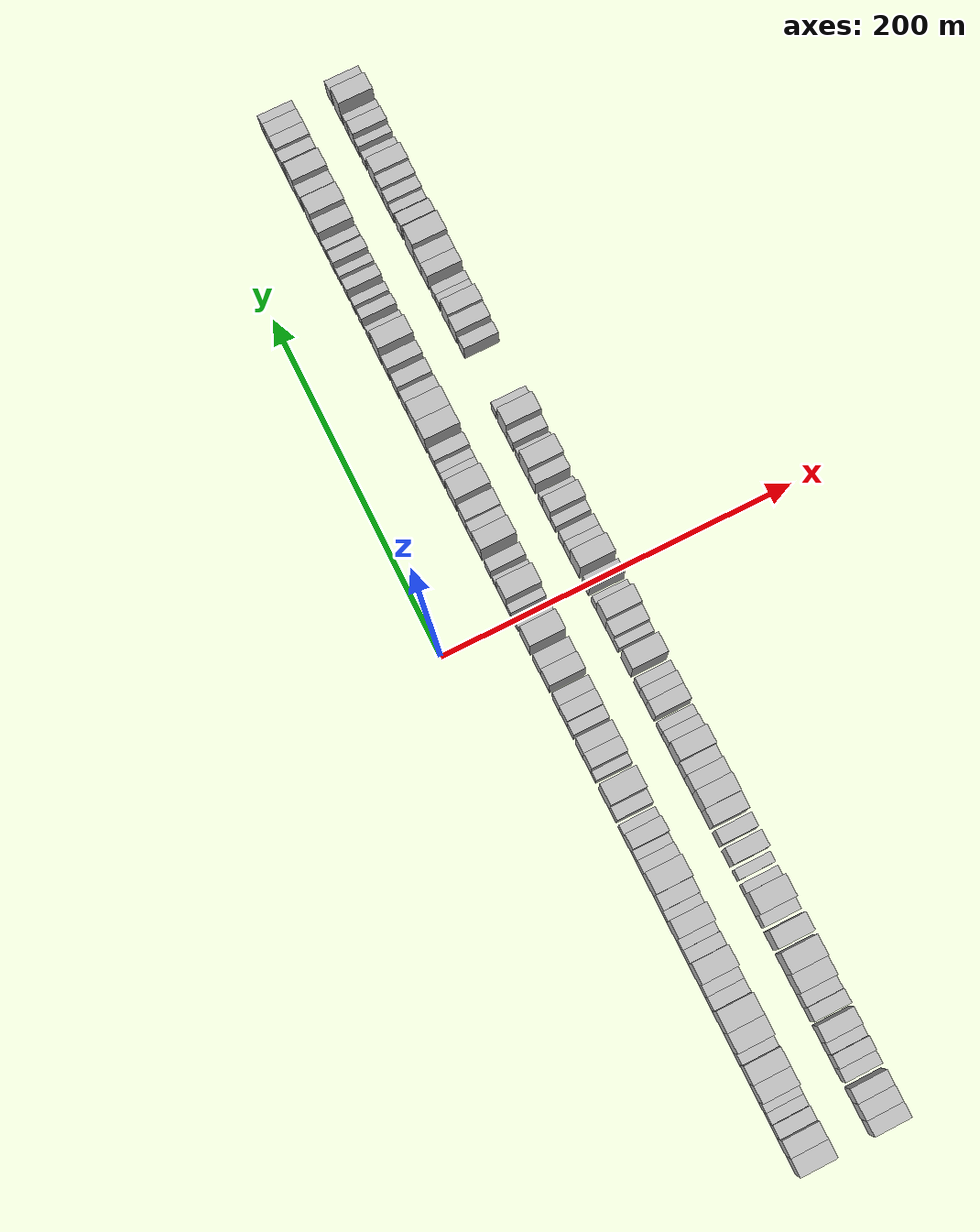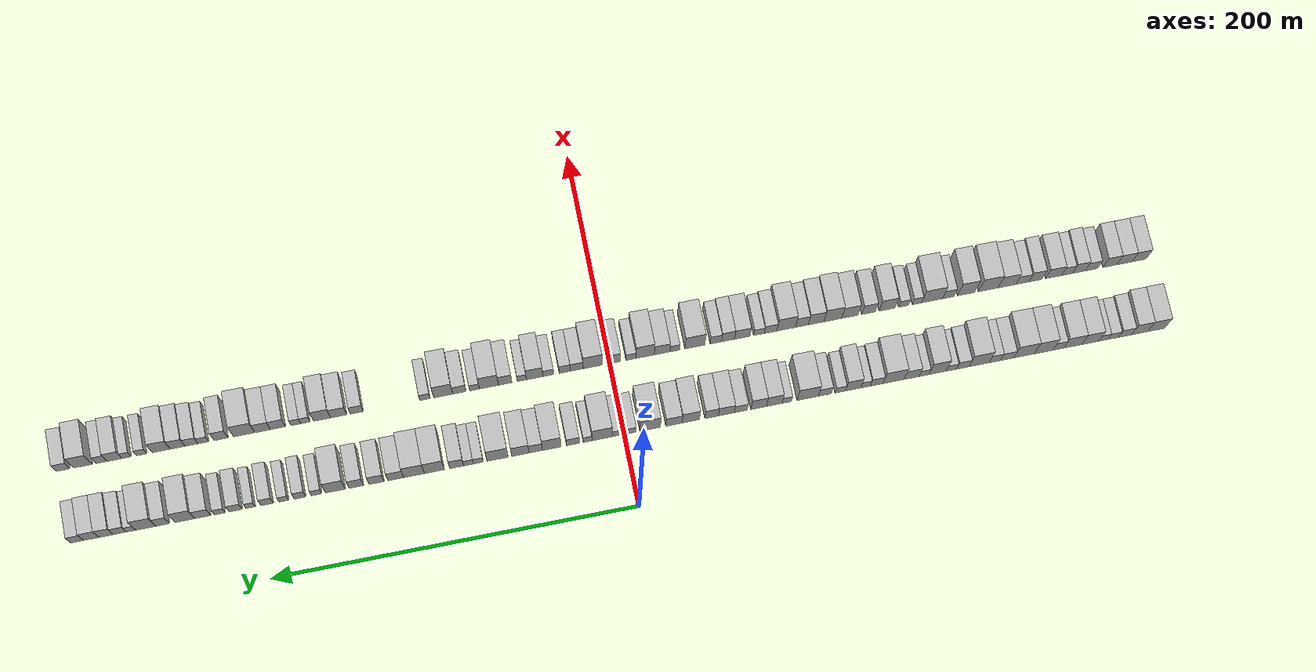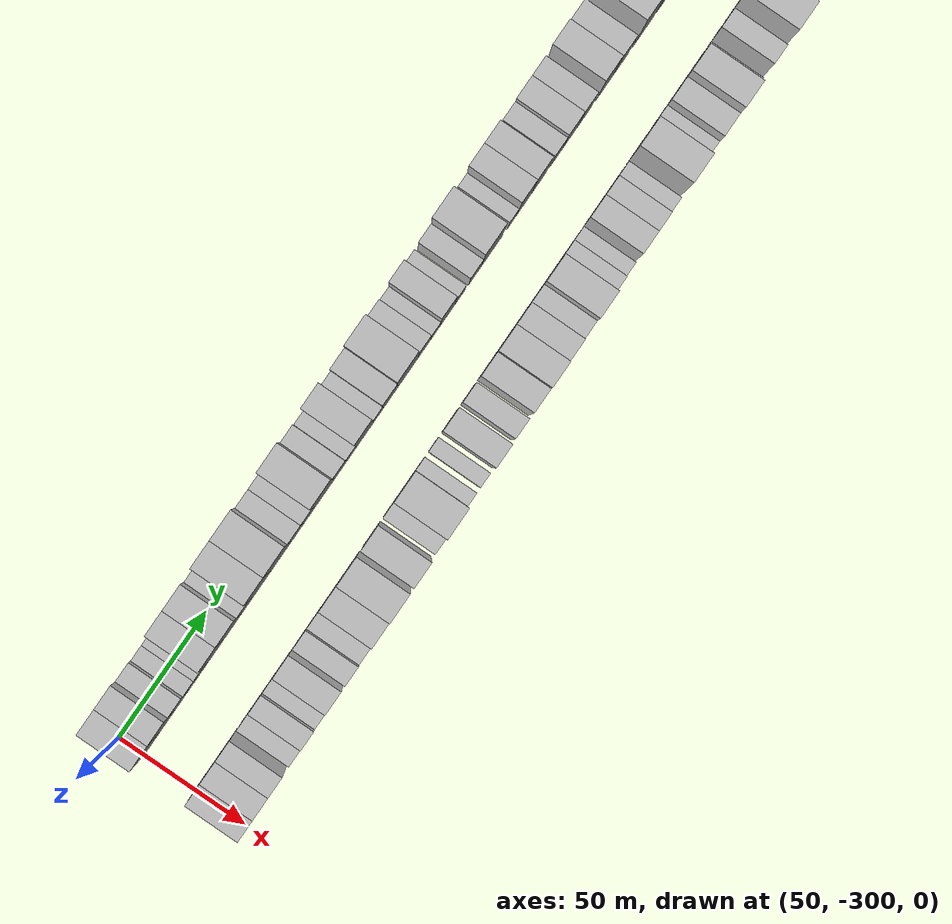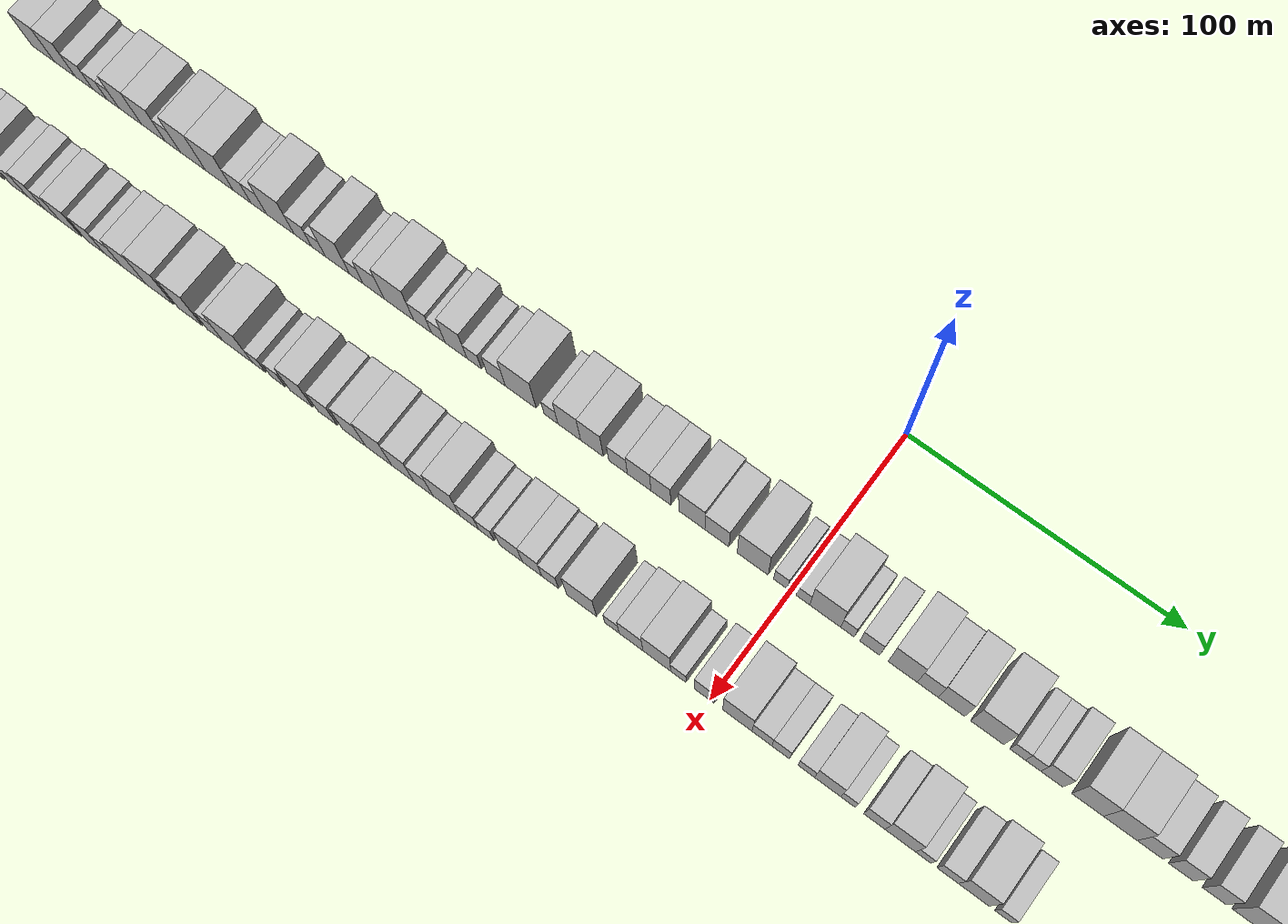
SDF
<sdf version="1.6">
 <world name="default">
  <scene>
   <sky><clouds><speed>12</speed></clouds></sky>
   <ambient>0.4 0.4 0.4 1</ambient>
   <background>0.7 0.7 0.7 1</background>
   <shadows>1</shadows>
  </scene>
  <gravity>0 0 -9.8066</gravity>
  <magnetic_field>6e-06 2.3e-05 -4.2e-05</magnetic_field>
  <physics default="0" name="default_physics" type="ode">
   <ode>
    <solver>
     <type>quick</type>
     <iters>10</iters>
     <sor>1.0</sor>
     <use_dynamic_moi_rescaling>0</use_dynamic_moi_rescaling>
    </solver>
    <constraints>
     <cfm>0</cfm>
     <erp>0.2</erp>
     <contact_max_correcting_vel>100</contact_max_correcting_vel>
     <contact_surface_layer>0.001</contact_surface_layer>
    </constraints>
   </ode>
   <max_step_size>0.004</max_step_size>
   <real_time_factor>1</real_time_factor>
   <real_time_update_rate>250</real_time_update_rate>
  </physics>
  <light name="sun" type="directional">
   <pose>0 0 10 0 0 0</pose>
   <diffuse>0.8 0.8 0.8 1</diffuse>
   <specular>0.2 0.2 0.2 1</specular>
   <attenuation>
    <range>1000</range>
    <constant>0.9</constant>
    <linear>0.01</linear>
    <quadratic>0.001</quadratic>
   </attenuation>
   <direction>-0.5 0.1 -0.9</direction>
  </light>
  <model name="building_1">
   <static>1</static>
   <pose>50.0000 -295.1970 0 0.000000 0.000000 0.000000</pose>
   <link name="link">
    <pose>0 0 10.50 0 0 0</pose>
    <collision name="collision"><geometry><box><size>20.0000 9.6060 21.0000</size></box></geometry></collision>
    <visual name="visual">
     <cast_shadows>0</cast_shadows>
     <geometry><box><size>20.0000 9.6060 21.0000</size></box></geometry>
     <material>
      <script>
       <uri>model://HANNAS_wall/materials/scripts</uri>
       <uri>model://HANNAS_wall/materials/textures</uri>
       <name>vrc/HANNAS_wall</name>
      </script>
     </material>
    </visual>
   </link>
  </model>
  <model name="building_2">
   <static>1</static>
   <pose>50.0000 -285.8825 0 0.000000 0.000000 0.000000</pose>
   <link name="link">
    <pose>0 0 10.50 0 0 0</pose>
    <collision name="collision"><geometry><box><size>20.0000 9.0231 21.0000</size></box></geometry></collision>
    <visual name="visual">
     <cast_shadows>0</cast_shadows>
     <geometry><box><size>20.0000 9.0231 21.0000</size></box></geometry>
     <material>
      <script>
       <uri>model://HANNAS_wall/materials/scripts</uri>
       <uri>model://HANNAS_wall/materials/textures</uri>
       <name>vrc/HANNAS_wall</name>
      </script>
     </material>
    </visual>
   </link>
  </model>
  <model name="building_3">
   <static>1</static>
   <pose>50.0000 -277.6992 0 0.000000 0.000000 0.000000</pose>
   <link name="link">
    <pose>0 0 7.50 0 0 0</pose>
    <collision name="collision"><geometry><box><size>20.0000 7.3435 15.0000</size></box></geometry></collision>
    <visual name="visual">
     <cast_shadows>0</cast_shadows>
     <geometry><box><size>20.0000 7.3435 15.0000</size></box></geometry>
     <material>
      <script>
       <uri>model://HANNAS_wall/materials/scripts</uri>
       <uri>model://HANNAS_wall/materials/textures</uri>
       <name>vrc/HANNAS_wall</name>
      </script>
     </material>
    </visual>
   </link>
  </model>
  <model name="building_4">
   <static>1</static>
   <pose>50.0000 -271.0660 0 0.000000 0.000000 0.000000</pose>
   <link name="link">
    <pose>0 0 6.00 0 0 0</pose>
    <collision name="collision"><geometry><box><size>20.0000 5.9230 12.0000</size></box></geometry></collision>
    <visual name="visual">
     <cast_shadows>0</cast_shadows>
     <geometry><box><size>20.0000 5.9230 12.0000</size></box></geometry>
     <material>
      <script>
       <uri>model://HANNAS_wall/materials/scripts</uri>
       <uri>model://HANNAS_wall/materials/textures</uri>
       <name>vrc/HANNAS_wall</name>
      </script>
     </material>
    </visual>
   </link>
  </model>
  <model name="building_5">
   <static>1</static>
   <pose>50.0000 -265.5462 0 0.000000 0.000000 0.000000</pose>
   <link name="link">
    <pose>0 0 6.00 0 0 0</pose>
    <collision name="collision"><geometry><box><size>20.0000 5.1166 12.0000</size></box></geometry></collision>
    <visual name="visual">
     <cast_shadows>0</cast_shadows>
     <geometry><box><size>20.0000 5.1166 12.0000</size></box></geometry>
     <material>
      <script>
       <uri>model://HANNAS_wall/materials/scripts</uri>
       <uri>model://HANNAS_wall/materials/textures</uri>
       <name>vrc/HANNAS_wall</name>
      </script>
     </material>
    </visual>
   </link>
  </model>
  <model name="building_6">
   <static>1</static>
   <pose>50.0000 -258.2183 0 0.000000 0.000000 0.000000</pose>
   <link name="link">
    <pose>0 0 10.50 0 0 0</pose>
    <collision name="collision"><geometry><box><size>20.0000 9.5392 21.0000</size></box></geometry></collision>
    <visual name="visual">
     <cast_shadows>0</cast_shadows>
     <geometry><box><size>20.0000 9.5392 21.0000</size></box></geometry>
     <material>
      <script>
       <uri>model://HANNAS_wall/materials/scripts</uri>
       <uri>model://HANNAS_wall/materials/textures</uri>
       <name>vrc/HANNAS_wall</name>
      </script>
     </material>
    </visual>
   </link>
  </model>
  <model name="building_7">
   <static>1</static>
   <pose>50.0000 -248.4536 0 0.000000 0.000000 0.000000</pose>
   <link name="link">
    <pose>0 0 10.50 0 0 0</pose>
    <collision name="collision"><geometry><box><size>20.0000 9.9902 21.0000</size></box></geometry></collision>
    <visual name="visual">
     <cast_shadows>0</cast_shadows>
     <geometry><box><size>20.0000 9.9902 21.0000</size></box></geometry>
     <material>
      <script>
       <uri>model://HANNAS_wall/materials/scripts</uri>
       <uri>model://HANNAS_wall/materials/textures</uri>
       <name>vrc/HANNAS_wall</name>
      </script>
     </material>
    </visual>
   </link>
  </model>
  <model name="building_8">
   <static>1</static>
   <pose>50.0000 -240.3835 0 0.000000 0.000000 0.000000</pose>
   <link name="link">
    <pose>0 0 7.50 0 0 0</pose>
    <collision name="collision"><geometry><box><size>20.0000 6.1500 15.0000</size></box></geometry></collision>
    <visual name="visual">
     <cast_shadows>0</cast_shadows>
     <geometry><box><size>20.0000 6.1500 15.0000</size></box></geometry>
     <material>
      <script>
       <uri>model://HANNAS_wall/materials/scripts</uri>
       <uri>model://HANNAS_wall/materials/textures</uri>
       <name>vrc/HANNAS_wall</name>
      </script>
     </material>
    </visual>
   </link>
  </model>
  <model name="building_9">
   <static>1</static>
   <pose>50.0000 -232.0826 0 0.000000 0.000000 0.000000</pose>
   <link name="link">
    <pose>0 0 12.00 0 0 0</pose>
    <collision name="collision"><geometry><box><size>20.0000 10.4518 24.0000</size></box></geometry></collision>
    <visual name="visual">
     <cast_shadows>0</cast_shadows>
     <geometry><box><size>20.0000 10.4518 24.0000</size></box></geometry>
     <material>
      <script>
       <uri>model://HANNAS_wall/materials/scripts</uri>
       <uri>model://HANNAS_wall/materials/textures</uri>
       <name>vrc/HANNAS_wall</name>
      </script>
     </material>
    </visual>
   </link>
  </model>
  <model name="building_10">
   <static>1</static>
   <pose>50.0000 -221.0790 0 0.000000 0.000000 0.000000</pose>
   <link name="link">
    <pose>0 0 12.00 0 0 0</pose>
    <collision name="collision"><geometry><box><size>20.0000 11.5555 24.0000</size></box></geometry></collision>
    <visual name="visual">
     <cast_shadows>0</cast_shadows>
     <geometry><box><size>20.0000 11.5555 24.0000</size></box></geometry>
     <material>
      <script>
       <uri>model://HANNAS_wall/materials/scripts</uri>
       <uri>model://HANNAS_wall/materials/textures</uri>
       <name>vrc/HANNAS_wall</name>
      </script>
     </material>
    </visual>
   </link>
  </model>
  <model name="building_11">
   <static>1</static>
   <pose>50.0000 -211.6667 0 0.000000 0.000000 0.000000</pose>
   <link name="link">
    <pose>0 0 7.50 0 0 0</pose>
    <collision name="collision"><geometry><box><size>20.0000 7.2691 15.0000</size></box></geometry></collision>
    <visual name="visual">
     <cast_shadows>0</cast_shadows>
     <geometry><box><size>20.0000 7.2691 15.0000</size></box></geometry>
     <material>
      <script>
       <uri>model://HANNAS_wall/materials/scripts</uri>
       <uri>model://HANNAS_wall/materials/textures</uri>
       <name>vrc/HANNAS_wall</name>
      </script>
     </material>
    </visual>
   </link>
  </model>
  <model name="building_12">
   <static>1</static>
   <pose>50.0000 -204.8449 0 0.000000 0.000000 0.000000</pose>
   <link name="link">
    <pose>0 0 7.50 0 0 0</pose>
    <collision name="collision"><geometry><box><size>20.0000 6.3745 15.0000</size></box></geometry></collision>
    <visual name="visual">
     <cast_shadows>0</cast_shadows>
     <geometry><box><size>20.0000 6.3745 15.0000</size></box></geometry>
     <material>
      <script>
       <uri>model://HANNAS_wall/materials/scripts</uri>
       <uri>model://HANNAS_wall/materials/textures</uri>
       <name>vrc/HANNAS_wall</name>
      </script>
     </material>
    </visual>
   </link>
  </model>
  <model name="building_13">
   <static>1</static>
   <pose>50.0000 -196.0315 0 0.000000 0.000000 0.000000</pose>
   <link name="link">
    <pose>0 0 12.00 0 0 0</pose>
    <collision name="collision"><geometry><box><size>20.0000 11.2523 24.0000</size></box></geometry></collision>
    <visual name="visual">
     <cast_shadows>0</cast_shadows>
     <geometry><box><size>20.0000 11.2523 24.0000</size></box></geometry>
     <material>
      <script>
       <uri>model://HANNAS_wall/materials/scripts</uri>
       <uri>model://HANNAS_wall/materials/textures</uri>
       <name>vrc/HANNAS_wall</name>
      </script>
     </material>
    </visual>
   </link>
  </model>
  <model name="building_14">
   <static>1</static>
   <pose>50.0000 -186.9027 0 0.000000 0.000000 0.000000</pose>
   <link name="link">
    <pose>0 0 7.50 0 0 0</pose>
    <collision name="collision"><geometry><box><size>20.0000 7.0055 15.0000</size></box></geometry></collision>
    <visual name="visual">
     <cast_shadows>0</cast_shadows>
     <geometry><box><size>20.0000 7.0055 15.0000</size></box></geometry>
     <material>
      <script>
       <uri>model://HANNAS_wall/materials/scripts</uri>
       <uri>model://HANNAS_wall/materials/textures</uri>
       <name>vrc/HANNAS_wall</name>
      </script>
     </material>
    </visual>
   </link>
  </model>
  <model name="building_15">
   <static>1</static>
   <pose>50.0000 -180.5846 0 0.000000 0.000000 0.000000</pose>
   <link name="link">
    <pose>0 0 6.00 0 0 0</pose>
    <collision name="collision"><geometry><box><size>20.0000 5.6305 12.0000</size></box></geometry></collision>
    <visual name="visual">
     <cast_shadows>0</cast_shadows>
     <geometry><box><size>20.0000 5.6305 12.0000</size></box></geometry>
     <material>
      <script>
       <uri>model://HANNAS_wall/materials/scripts</uri>
       <uri>model://HANNAS_wall/materials/textures</uri>
       <name>vrc/HANNAS_wall</name>
      </script>
     </material>
    </visual>
   </link>
  </model>
  <model name="building_16">
   <static>1</static>
   <pose>50.0000 -172.9262 0 0.000000 0.000000 0.000000</pose>
   <link name="link">
    <pose>0 0 12.00 0 0 0</pose>
    <collision name="collision"><geometry><box><size>20.0000 9.6863 24.0000</size></box></geometry></collision>
    <visual name="visual">
     <cast_shadows>0</cast_shadows>
     <geometry><box><size>20.0000 9.6863 24.0000</size></box></geometry>
     <material>
      <script>
       <uri>model://HANNAS_wall/materials/scripts</uri>
       <uri>model://HANNAS_wall/materials/textures</uri>
       <name>vrc/HANNAS_wall</name>
      </script>
     </material>
    </visual>
   </link>
  </model>
  <model name="building_17">
   <static>1</static>
   <pose>50.0000 -165.3919 0 0.000000 0.000000 0.000000</pose>
   <link name="link">
    <pose>0 0 6.00 0 0 0</pose>
    <collision name="collision"><geometry><box><size>20.0000 5.3823 12.0000</size></box></geometry></collision>
    <visual name="visual">
     <cast_shadows>0</cast_shadows>
     <geometry><box><size>20.0000 5.3823 12.0000</size></box></geometry>
     <material>
      <script>
       <uri>model://HANNAS_wall/materials/scripts</uri>
       <uri>model://HANNAS_wall/materials/textures</uri>
       <name>vrc/HANNAS_wall</name>
      </script>
     </material>
    </visual>
   </link>
  </model>
  <model name="building_18">
   <static>1</static>
   <pose>50.0000 -158.5544 0 0.000000 0.000000 0.000000</pose>
   <link name="link">
    <pose>0 0 9.00 0 0 0</pose>
    <collision name="collision"><geometry><box><size>20.0000 8.2926 18.0000</size></box></geometry></collision>
    <visual name="visual">
     <cast_shadows>0</cast_shadows>
     <geometry><box><size>20.0000 8.2926 18.0000</size></box></geometry>
     <material>
      <script>
       <uri>model://HANNAS_wall/materials/scripts</uri>
       <uri>model://HANNAS_wall/materials/textures</uri>
       <name>vrc/HANNAS_wall</name>
      </script>
     </material>
    </visual>
   </link>
  </model>
  <model name="building_19">
   <static>1</static>
   <pose>50.0000 -148.5214 0 0.000000 0.000000 0.000000</pose>
   <link name="link">
    <pose>0 0 12.00 0 0 0</pose>
    <collision name="collision"><geometry><box><size>20.0000 11.7735 24.0000</size></box></geometry></collision>
    <visual name="visual">
     <cast_shadows>0</cast_shadows>
     <geometry><box><size>20.0000 11.7735 24.0000</size></box></geometry>
     <material>
      <script>
       <uri>model://HANNAS_wall/materials/scripts</uri>
       <uri>model://HANNAS_wall/materials/textures</uri>
       <name>vrc/HANNAS_wall</name>
      </script>
     </material>
    </visual>
   </link>
  </model>
  <model name="building_20">
   <static>1</static>
   <pose>50.0000 -139.1447 0 0.000000 0.000000 0.000000</pose>
   <link name="link">
    <pose>0 0 7.50 0 0 0</pose>
    <collision name="collision"><geometry><box><size>20.0000 6.9799 15.0000</size></box></geometry></collision>
    <visual name="visual">
     <cast_shadows>0</cast_shadows>
     <geometry><box><size>20.0000 6.9799 15.0000</size></box></geometry>
     <material>
      <script>
       <uri>model://HANNAS_wall/materials/scripts</uri>
       <uri>model://HANNAS_wall/materials/textures</uri>
       <name>vrc/HANNAS_wall</name>
      </script>
     </material>
    </visual>
   </link>
  </model>
  <model name="building_21">
   <static>1</static>
   <pose>50.0000 -132.9606 0 0.000000 0.000000 0.000000</pose>
   <link name="link">
    <pose>0 0 6.00 0 0 0</pose>
    <collision name="collision"><geometry><box><size>20.0000 5.3883 12.0000</size></box></geometry></collision>
    <visual name="visual">
     <cast_shadows>0</cast_shadows>
     <geometry><box><size>20.0000 5.3883 12.0000</size></box></geometry>
     <material>
      <script>
       <uri>model://HANNAS_wall/materials/scripts</uri>
       <uri>model://HANNAS_wall/materials/textures</uri>
       <name>vrc/HANNAS_wall</name>
      </script>
     </material>
    </visual>
   </link>
  </model>
  <model name="building_22">
   <static>1</static>
   <pose>50.0000 -126.0294 0 0.000000 0.000000 0.000000</pose>
   <link name="link">
    <pose>0 0 10.50 0 0 0</pose>
    <collision name="collision"><geometry><box><size>20.0000 8.4740 21.0000</size></box></geometry></collision>
    <visual name="visual">
     <cast_shadows>0</cast_shadows>
     <geometry><box><size>20.0000 8.4740 21.0000</size></box></geometry>
     <material>
      <script>
       <uri>model://HANNAS_wall/materials/scripts</uri>
       <uri>model://HANNAS_wall/materials/textures</uri>
       <name>vrc/HANNAS_wall</name>
      </script>
     </material>
    </visual>
   </link>
  </model>
  <model name="building_23">
   <static>1</static>
   <pose>50.0000 -118.9303 0 0.000000 0.000000 0.000000</pose>
   <link name="link">
    <pose>0 0 6.00 0 0 0</pose>
    <collision name="collision"><geometry><box><size>20.0000 5.7242 12.0000</size></box></geometry></collision>
    <visual name="visual">
     <cast_shadows>0</cast_shadows>
     <geometry><box><size>20.0000 5.7242 12.0000</size></box></geometry>
     <material>
      <script>
       <uri>model://HANNAS_wall/materials/scripts</uri>
       <uri>model://HANNAS_wall/materials/textures</uri>
       <name>vrc/HANNAS_wall</name>
      </script>
     </material>
    </visual>
   </link>
  </model>
  <model name="building_24">
   <static>1</static>
   <pose>50.0000 -110.4495 0 0.000000 0.000000 0.000000</pose>
   <link name="link">
    <pose>0 0 7.50 0 0 0</pose>
    <collision name="collision"><geometry><box><size>20.0000 7.2374 15.0000</size></box></geometry></collision>
    <visual name="visual">
     <cast_shadows>0</cast_shadows>
     <geometry><box><size>20.0000 7.2374 15.0000</size></box></geometry>
     <material>
      <script>
       <uri>model://HANNAS_wall/materials/scripts</uri>
       <uri>model://HANNAS_wall/materials/textures</uri>
       <name>vrc/HANNAS_wall</name>
      </script>
     </material>
    </visual>
   </link>
  </model>
  <model name="building_25">
   <static>1</static>
   <pose>50.0000 -100.9167 0 0.000000 0.000000 0.000000</pose>
   <link name="link">
    <pose>0 0 12.00 0 0 0</pose>
    <collision name="collision"><geometry><box><size>20.0000 11.8284 24.0000</size></box></geometry></collision>
    <visual name="visual">
     <cast_shadows>0</cast_shadows>
     <geometry><box><size>20.0000 11.8284 24.0000</size></box></geometry>
     <material>
      <script>
       <uri>model://HANNAS_wall/materials/scripts</uri>
       <uri>model://HANNAS_wall/materials/textures</uri>
       <name>vrc/HANNAS_wall</name>
      </script>
     </material>
    </visual>
   </link>
  </model>
  <model name="building_26">
   <static>1</static>
   <pose>50.0000 -89.3581 0 0.000000 0.000000 0.000000</pose>
   <link name="link">
    <pose>0 0 6.00 0 0 0</pose>
    <collision name="collision"><geometry><box><size>20.0000 5.2886 12.0000</size></box></geometry></collision>
    <visual name="visual">
     <cast_shadows>0</cast_shadows>
     <geometry><box><size>20.0000 5.2886 12.0000</size></box></geometry>
     <material>
      <script>
       <uri>model://HANNAS_wall/materials/scripts</uri>
       <uri>model://HANNAS_wall/materials/textures</uri>
       <name>vrc/HANNAS_wall</name>
      </script>
     </material>
    </visual>
   </link>
  </model>
  <model name="building_27">
   <static>1</static>
   <pose>50.0000 -82.3834 0 0.000000 0.000000 0.000000</pose>
   <link name="link">
    <pose>0 0 10.50 0 0 0</pose>
    <collision name="collision"><geometry><box><size>20.0000 8.6609 21.0000</size></box></geometry></collision>
    <visual name="visual">
     <cast_shadows>0</cast_shadows>
     <geometry><box><size>20.0000 8.6609 21.0000</size></box></geometry>
     <material>
      <script>
       <uri>model://HANNAS_wall/materials/scripts</uri>
       <uri>model://HANNAS_wall/materials/textures</uri>
       <name>vrc/HANNAS_wall</name>
      </script>
     </material>
    </visual>
   </link>
  </model>
  <model name="building_28">
   <static>1</static>
   <pose>50.0000 -73.7411 0 0.000000 0.000000 0.000000</pose>
   <link name="link">
    <pose>0 0 10.50 0 0 0</pose>
    <collision name="collision"><geometry><box><size>20.0000 8.6237 21.0000</size></box></geometry></collision>
    <visual name="visual">
     <cast_shadows>0</cast_shadows>
     <geometry><box><size>20.0000 8.6237 21.0000</size></box></geometry>
     <material>
      <script>
       <uri>model://HANNAS_wall/materials/scripts</uri>
       <uri>model://HANNAS_wall/materials/textures</uri>
       <name>vrc/HANNAS_wall</name>
      </script>
     </material>
    </visual>
   </link>
  </model>
  <model name="building_29">
   <static>1</static>
   <pose>50.0000 -63.8989 0 0.000000 0.000000 0.000000</pose>
   <link name="link">
    <pose>0 0 7.50 0 0 0</pose>
    <collision name="collision"><geometry><box><size>20.0000 7.0606 15.0000</size></box></geometry></collision>
    <visual name="visual">
     <cast_shadows>0</cast_shadows>
     <geometry><box><size>20.0000 7.0606 15.0000</size></box></geometry>
     <material>
      <script>
       <uri>model://HANNAS_wall/materials/scripts</uri>
       <uri>model://HANNAS_wall/materials/textures</uri>
       <name>vrc/HANNAS_wall</name>
      </script>
     </material>
    </visual>
   </link>
  </model>
  <model name="building_30">
   <static>1</static>
   <pose>50.0000 -55.9622 0 0.000000 0.000000 0.000000</pose>
   <link name="link">
    <pose>0 0 9.00 0 0 0</pose>
    <collision name="collision"><geometry><box><size>20.0000 8.8129 18.0000</size></box></geometry></collision>
    <visual name="visual">
     <cast_shadows>0</cast_shadows>
     <geometry><box><size>20.0000 8.8129 18.0000</size></box></geometry>
     <material>
      <script>
       <uri>model://HANNAS_wall/materials/scripts</uri>
       <uri>model://HANNAS_wall/materials/textures</uri>
       <name>vrc/HANNAS_wall</name>
      </script>
     </material>
    </visual>
   </link>
  </model>
  <model name="building_31">
   <static>1</static>
   <pose>50.0000 -47.8337 0 0.000000 0.000000 0.000000</pose>
   <link name="link">
    <pose>0 0 9.00 0 0 0</pose>
    <collision name="collision"><geometry><box><size>20.0000 7.4441 18.0000</size></box></geometry></collision>
    <visual name="visual">
     <cast_shadows>0</cast_shadows>
     <geometry><box><size>20.0000 7.4441 18.0000</size></box></geometry>
     <material>
      <script>
       <uri>model://HANNAS_wall/materials/scripts</uri>
       <uri>model://HANNAS_wall/materials/textures</uri>
       <name>vrc/HANNAS_wall</name>
      </script>
     </material>
    </visual>
   </link>
  </model>
  <model name="building_32">
   <static>1</static>
   <pose>50.0000 -36.3141 0 0.000000 0.000000 0.000000</pose>
   <link name="link">
    <pose>0 0 10.50 0 0 0</pose>
    <collision name="collision"><geometry><box><size>20.0000 9.5950 21.0000</size></box></geometry></collision>
    <visual name="visual">
     <cast_shadows>0</cast_shadows>
     <geometry><box><size>20.0000 9.5950 21.0000</size></box></geometry>
     <material>
      <script>
       <uri>model://HANNAS_wall/materials/scripts</uri>
       <uri>model://HANNAS_wall/materials/textures</uri>
       <name>vrc/HANNAS_wall</name>
      </script>
     </material>
    </visual>
   </link>
  </model>
  <model name="building_33">
   <static>1</static>
   <pose>50.0000 -27.0605 0 0.000000 0.000000 0.000000</pose>
   <link name="link">
    <pose>0 0 9.00 0 0 0</pose>
    <collision name="collision"><geometry><box><size>20.0000 8.9123 18.0000</size></box></geometry></collision>
    <visual name="visual">
     <cast_shadows>0</cast_shadows>
     <geometry><box><size>20.0000 8.9123 18.0000</size></box></geometry>
     <material>
      <script>
       <uri>model://HANNAS_wall/materials/scripts</uri>
       <uri>model://HANNAS_wall/materials/textures</uri>
       <name>vrc/HANNAS_wall</name>
      </script>
     </material>
    </visual>
   </link>
  </model>
  <model name="building_34">
   <static>1</static>
   <pose>50.0000 -13.9487 0 0.000000 0.000000 0.000000</pose>
   <link name="link">
    <pose>0 0 12.00 0 0 0</pose>
    <collision name="collision"><geometry><box><size>20.0000 11.3113 24.0000</size></box></geometry></collision>
    <visual name="visual">
     <cast_shadows>0</cast_shadows>
     <geometry><box><size>20.0000 11.3113 24.0000</size></box></geometry>
     <material>
      <script>
       <uri>model://HANNAS_wall/materials/scripts</uri>
       <uri>model://HANNAS_wall/materials/textures</uri>
       <name>vrc/HANNAS_wall</name>
      </script>
     </material>
    </visual>
   </link>
  </model>
  <model name="building_35">
   <static>1</static>
   <pose>50.0000 -3.7508 0 0.000000 0.000000 0.000000</pose>
   <link name="link">
    <pose>0 0 6.00 0 0 0</pose>
    <collision name="collision"><geometry><box><size>20.0000 5.0844 12.0000</size></box></geometry></collision>
    <visual name="visual">
     <cast_shadows>0</cast_shadows>
     <geometry><box><size>20.0000 5.0844 12.0000</size></box></geometry>
     <material>
      <script>
       <uri>model://HANNAS_wall/materials/scripts</uri>
       <uri>model://HANNAS_wall/materials/textures</uri>
       <name>vrc/HANNAS_wall</name>
      </script>
     </material>
    </visual>
   </link>
  </model>
  <model name="building_36">
   <static>1</static>
   <pose>50.0000 4.3104 0 0.000000 0.000000 0.000000</pose>
   <link name="link">
    <pose>0 0 6.00 0 0 0</pose>
    <collision name="collision"><geometry><box><size>20.0000 5.0379 12.0000</size></box></geometry></collision>
    <visual name="visual">
     <cast_shadows>0</cast_shadows>
     <geometry><box><size>20.0000 5.0379 12.0000</size></box></geometry>
     <material>
      <script>
       <uri>model://HANNAS_wall/materials/scripts</uri>
       <uri>model://HANNAS_wall/materials/textures</uri>
       <name>vrc/HANNAS_wall</name>
      </script>
     </material>
    </visual>
   </link>
  </model>
  <model name="building_37">
   <static>1</static>
   <pose>50.0000 12.4003 0 0.000000 0.000000 0.000000</pose>
   <link name="link">
    <pose>0 0 12.00 0 0 0</pose>
    <collision name="collision"><geometry><box><size>20.0000 11.1420 24.0000</size></box></geometry></collision>
    <visual name="visual">
     <cast_shadows>0</cast_shadows>
     <geometry><box><size>20.0000 11.1420 24.0000</size></box></geometry>
     <material>
      <script>
       <uri>model://HANNAS_wall/materials/scripts</uri>
       <uri>model://HANNAS_wall/materials/textures</uri>
       <name>vrc/HANNAS_wall</name>
      </script>
     </material>
    </visual>
   </link>
  </model>
  <model name="building_38">
   <static>1</static>
   <pose>50.0000 20.3887 0 0.000000 0.000000 0.000000</pose>
   <link name="link">
    <pose>0 0 6.00 0 0 0</pose>
    <collision name="collision"><geometry><box><size>20.0000 4.8348 12.0000</size></box></geometry></collision>
    <visual name="visual">
     <cast_shadows>0</cast_shadows>
     <geometry><box><size>20.0000 4.8348 12.0000</size></box></geometry>
     <material>
      <script>
       <uri>model://HANNAS_wall/materials/scripts</uri>
       <uri>model://HANNAS_wall/materials/textures</uri>
       <name>vrc/HANNAS_wall</name>
      </script>
     </material>
    </visual>
   </link>
  </model>
  <model name="building_39">
   <static>1</static>
   <pose>50.0000 28.3555 0 0.000000 0.000000 0.000000</pose>
   <link name="link">
    <pose>0 0 7.50 0 0 0</pose>
    <collision name="collision"><geometry><box><size>20.0000 7.0989 15.0000</size></box></geometry></collision>
    <visual name="visual">
     <cast_shadows>0</cast_shadows>
     <geometry><box><size>20.0000 7.0989 15.0000</size></box></geometry>
     <material>
      <script>
       <uri>model://HANNAS_wall/materials/scripts</uri>
       <uri>model://HANNAS_wall/materials/textures</uri>
       <name>vrc/HANNAS_wall</name>
      </script>
     </material>
    </visual>
   </link>
  </model>
  <model name="building_40">
   <static>1</static>
   <pose>50.0000 40.0406 0 0.000000 0.000000 0.000000</pose>
   <link name="link">
    <pose>0 0 12.00 0 0 0</pose>
    <collision name="collision"><geometry><box><size>20.0000 10.2713 24.0000</size></box></geometry></collision>
    <visual name="visual">
     <cast_shadows>0</cast_shadows>
     <geometry><box><size>20.0000 10.2713 24.0000</size></box></geometry>
     <material>
      <script>
       <uri>model://HANNAS_wall/materials/scripts</uri>
       <uri>model://HANNAS_wall/materials/textures</uri>
       <name>vrc/HANNAS_wall</name>
      </script>
     </material>
    </visual>
   </link>
  </model>
  <model name="building_41">
   <static>1</static>
   <pose>50.0000 48.8296 0 0.000000 0.000000 0.000000</pose>
   <link name="link">
    <pose>0 0 9.00 0 0 0</pose>
    <collision name="collision"><geometry><box><size>20.0000 7.3065 18.0000</size></box></geometry></collision>
    <visual name="visual">
     <cast_shadows>0</cast_shadows>
     <geometry><box><size>20.0000 7.3065 18.0000</size></box></geometry>
     <material>
      <script>
       <uri>model://HANNAS_wall/materials/scripts</uri>
       <uri>model://HANNAS_wall/materials/textures</uri>
       <name>vrc/HANNAS_wall</name>
      </script>
     </material>
    </visual>
   </link>
  </model>
  <model name="building_42">
   <static>1</static>
   <pose>50.0000 57.1725 0 0.000000 0.000000 0.000000</pose>
   <link name="link">
    <pose>0 0 10.50 0 0 0</pose>
    <collision name="collision"><geometry><box><size>20.0000 9.3794 21.0000</size></box></geometry></collision>
    <visual name="visual">
     <cast_shadows>0</cast_shadows>
     <geometry><box><size>20.0000 9.3794 21.0000</size></box></geometry>
     <material>
      <script>
       <uri>model://HANNAS_wall/materials/scripts</uri>
       <uri>model://HANNAS_wall/materials/textures</uri>
       <name>vrc/HANNAS_wall</name>
      </script>
     </material>
    </visual>
   </link>
  </model>
  <model name="building_43">
   <static>1</static>
   <pose>50.0000 69.6522 0 0.000000 0.000000 0.000000</pose>
   <link name="link">
    <pose>0 0 12.00 0 0 0</pose>
    <collision name="collision"><geometry><box><size>20.0000 11.5799 24.0000</size></box></geometry></collision>
    <visual name="visual">
     <cast_shadows>0</cast_shadows>
     <geometry><box><size>20.0000 11.5799 24.0000</size></box></geometry>
     <material>
      <script>
       <uri>model://HANNAS_wall/materials/scripts</uri>
       <uri>model://HANNAS_wall/materials/textures</uri>
       <name>vrc/HANNAS_wall</name>
      </script>
     </material>
    </visual>
   </link>
  </model>
  <model name="building_44">
   <static>1</static>
   <pose>50.0000 80.1559 0 0.000000 0.000000 0.000000</pose>
   <link name="link">
    <pose>0 0 6.00 0 0 0</pose>
    <collision name="collision"><geometry><box><size>20.0000 5.4277 12.0000</size></box></geometry></collision>
    <visual name="visual">
     <cast_shadows>0</cast_shadows>
     <geometry><box><size>20.0000 5.4277 12.0000</size></box></geometry>
     <material>
      <script>
       <uri>model://HANNAS_wall/materials/scripts</uri>
       <uri>model://HANNAS_wall/materials/textures</uri>
       <name>vrc/HANNAS_wall</name>
      </script>
     </material>
    </visual>
   </link>
  </model>
  <model name="building_45">
   <static>1</static>
   <pose>50.0000 85.5039 0 0.000000 0.000000 0.000000</pose>
   <link name="link">
    <pose>0 0 6.00 0 0 0</pose>
    <collision name="collision"><geometry><box><size>20.0000 5.2683 12.0000</size></box></geometry></collision>
    <visual name="visual">
     <cast_shadows>0</cast_shadows>
     <geometry><box><size>20.0000 5.2683 12.0000</size></box></geometry>
     <material>
      <script>
       <uri>model://HANNAS_wall/materials/scripts</uri>
       <uri>model://HANNAS_wall/materials/textures</uri>
       <name>vrc/HANNAS_wall</name>
      </script>
     </material>
    </visual>
   </link>
  </model>
  <model name="building_46">
   <static>1</static>
   <pose>50.0000 91.9332 0 0.000000 0.000000 0.000000</pose>
   <link name="link">
    <pose>0 0 9.00 0 0 0</pose>
    <collision name="collision"><geometry><box><size>20.0000 7.5904 18.0000</size></box></geometry></collision>
    <visual name="visual">
     <cast_shadows>0</cast_shadows>
     <geometry><box><size>20.0000 7.5904 18.0000</size></box></geometry>
     <material>
      <script>
       <uri>model://HANNAS_wall/materials/scripts</uri>
       <uri>model://HANNAS_wall/materials/textures</uri>
       <name>vrc/HANNAS_wall</name>
      </script>
     </material>
    </visual>
   </link>
  </model>
  <model name="building_47">
   <static>1</static>
   <pose>50.0000 104.1379 0 0.000000 0.000000 0.000000</pose>
   <link name="link">
    <pose>0 0 12.00 0 0 0</pose>
    <collision name="collision"><geometry><box><size>20.0000 10.8189 24.0000</size></box></geometry></collision>
    <visual name="visual">
     <cast_shadows>0</cast_shadows>
     <geometry><box><size>20.0000 10.8189 24.0000</size></box></geometry>
     <material>
      <script>
       <uri>model://HANNAS_wall/materials/scripts</uri>
       <uri>model://HANNAS_wall/materials/textures</uri>
       <name>vrc/HANNAS_wall</name>
      </script>
     </material>
    </visual>
   </link>
  </model>
  <model name="building_48">
   <static>1</static>
   <pose>50.0000 115.2195 0 0.000000 0.000000 0.000000</pose>
   <link name="link">
    <pose>0 0 12.00 0 0 0</pose>
    <collision name="collision"><geometry><box><size>20.0000 11.3442 24.0000</size></box></geometry></collision>
    <visual name="visual">
     <cast_shadows>0</cast_shadows>
     <geometry><box><size>20.0000 11.3442 24.0000</size></box></geometry>
     <material>
      <script>
       <uri>model://HANNAS_wall/materials/scripts</uri>
       <uri>model://HANNAS_wall/materials/textures</uri>
       <name>vrc/HANNAS_wall</name>
      </script>
     </material>
    </visual>
   </link>
  </model>
  <model name="building_49">
   <static>1</static>
   <pose>50.0000 125.1964 0 0.000000 0.000000 0.000000</pose>
   <link name="link">
    <pose>0 0 9.00 0 0 0</pose>
    <collision name="collision"><geometry><box><size>20.0000 8.6096 18.0000</size></box></geometry></collision>
    <visual name="visual">
     <cast_shadows>0</cast_shadows>
     <geometry><box><size>20.0000 8.6096 18.0000</size></box></geometry>
     <material>
      <script>
       <uri>model://HANNAS_wall/materials/scripts</uri>
       <uri>model://HANNAS_wall/materials/textures</uri>
       <name>vrc/HANNAS_wall</name>
      </script>
     </material>
    </visual>
   </link>
  </model>
  <model name="building_50">
   <static>1</static>
   <pose>50.0000 135.5839 0 0.000000 0.000000 0.000000</pose>
   <link name="link">
    <pose>0 0 9.00 0 0 0</pose>
    <collision name="collision"><geometry><box><size>20.0000 8.1655 18.0000</size></box></geometry></collision>
    <visual name="visual">
     <cast_shadows>0</cast_shadows>
     <geometry><box><size>20.0000 8.1655 18.0000</size></box></geometry>
     <material>
      <script>
       <uri>model://HANNAS_wall/materials/scripts</uri>
       <uri>model://HANNAS_wall/materials/textures</uri>
       <name>vrc/HANNAS_wall</name>
      </script>
     </material>
    </visual>
   </link>
  </model>
  <model name="building_51">
   <static>1</static>
   <pose>50.0000 146.5986 0 0.000000 0.000000 0.000000</pose>
   <link name="link">
    <pose>0 0 9.00 0 0 0</pose>
    <collision name="collision"><geometry><box><size>20.0000 7.8638 18.0000</size></box></geometry></collision>
    <visual name="visual">
     <cast_shadows>0</cast_shadows>
     <geometry><box><size>20.0000 7.8638 18.0000</size></box></geometry>
     <material>
      <script>
       <uri>model://HANNAS_wall/materials/scripts</uri>
       <uri>model://HANNAS_wall/materials/textures</uri>
       <name>vrc/HANNAS_wall</name>
      </script>
     </material>
    </visual>
   </link>
  </model>
  <model name="building_52">
   <static>1</static>
   <pose>50.0000 157.9453 0 0.000000 0.000000 0.000000</pose>
   <link name="link">
    <pose>0 0 12.00 0 0 0</pose>
    <collision name="collision"><geometry><box><size>20.0000 10.8296 24.0000</size></box></geometry></collision>
    <visual name="visual">
     <cast_shadows>0</cast_shadows>
     <geometry><box><size>20.0000 10.8296 24.0000</size></box></geometry>
     <material>
      <script>
       <uri>model://HANNAS_wall/materials/scripts</uri>
       <uri>model://HANNAS_wall/materials/textures</uri>
       <name>vrc/HANNAS_wall</name>
      </script>
     </material>
    </visual>
   </link>
  </model>
  <model name="building_53">
   <static>1</static>
   <pose>50.0000 168.1985 0 0.000000 0.000000 0.000000</pose>
   <link name="link">
    <pose>0 0 6.00 0 0 0</pose>
    <collision name="collision"><geometry><box><size>20.0000 5.6769 12.0000</size></box></geometry></collision>
    <visual name="visual">
     <cast_shadows>0</cast_shadows>
     <geometry><box><size>20.0000 5.6769 12.0000</size></box></geometry>
     <material>
      <script>
       <uri>model://HANNAS_wall/materials/scripts</uri>
       <uri>model://HANNAS_wall/materials/textures</uri>
       <name>vrc/HANNAS_wall</name>
      </script>
     </material>
    </visual>
   </link>
  </model>
  <model name="building_54">
   <static>1</static>
   <pose>50.0000 177.1608 0 0.000000 0.000000 0.000000</pose>
   <link name="link">
    <pose>0 0 7.50 0 0 0</pose>
    <collision name="collision"><geometry><box><size>20.0000 6.2477 15.0000</size></box></geometry></collision>
    <visual name="visual">
     <cast_shadows>0</cast_shadows>
     <geometry><box><size>20.0000 6.2477 15.0000</size></box></geometry>
     <material>
      <script>
       <uri>model://HANNAS_wall/materials/scripts</uri>
       <uri>model://HANNAS_wall/materials/textures</uri>
       <name>vrc/HANNAS_wall</name>
      </script>
     </material>
    </visual>
   </link>
  </model>
  <model name="building_55">
   <static>1</static>
   <pose>50.0000 185.9469 0 0.000000 0.000000 0.000000</pose>
   <link name="link">
    <pose>0 0 6.00 0 0 0</pose>
    <collision name="collision"><geometry><box><size>20.0000 5.3243 12.0000</size></box></geometry></collision>
    <visual name="visual">
     <cast_shadows>0</cast_shadows>
     <geometry><box><size>20.0000 5.3243 12.0000</size></box></geometry>
     <material>
      <script>
       <uri>model://HANNAS_wall/materials/scripts</uri>
       <uri>model://HANNAS_wall/materials/textures</uri>
       <name>vrc/HANNAS_wall</name>
      </script>
     </material>
    </visual>
   </link>
  </model>
  <model name="building_56">
   <static>1</static>
   <pose>50.0000 194.9970 0 0.000000 0.000000 0.000000</pose>
   <link name="link">
    <pose>0 0 7.50 0 0 0</pose>
    <collision name="collision"><geometry><box><size>20.0000 6.7760 15.0000</size></box></geometry></collision>
    <visual name="visual">
     <cast_shadows>0</cast_shadows>
     <geometry><box><size>20.0000 6.7760 15.0000</size></box></geometry>
     <material>
      <script>
       <uri>model://HANNAS_wall/materials/scripts</uri>
       <uri>model://HANNAS_wall/materials/textures</uri>
       <name>vrc/HANNAS_wall</name>
      </script>
     </material>
    </visual>
   </link>
  </model>
  <model name="building_57">
   <static>1</static>
   <pose>50.0000 203.9199 0 0.000000 0.000000 0.000000</pose>
   <link name="link">
    <pose>0 0 6.00 0 0 0</pose>
    <collision name="collision"><geometry><box><size>20.0000 5.0697 12.0000</size></box></geometry></collision>
    <visual name="visual">
     <cast_shadows>0</cast_shadows>
     <geometry><box><size>20.0000 5.0697 12.0000</size></box></geometry>
     <material>
      <script>
       <uri>model://HANNAS_wall/materials/scripts</uri>
       <uri>model://HANNAS_wall/materials/textures</uri>
       <name>vrc/HANNAS_wall</name>
      </script>
     </material>
    </visual>
   </link>
  </model>
  <model name="building_58">
   <static>1</static>
   <pose>50.0000 212.0440 0 0.000000 0.000000 0.000000</pose>
   <link name="link">
    <pose>0 0 7.50 0 0 0</pose>
    <collision name="collision"><geometry><box><size>20.0000 7.1785 15.0000</size></box></geometry></collision>
    <visual name="visual">
     <cast_shadows>0</cast_shadows>
     <geometry><box><size>20.0000 7.1785 15.0000</size></box></geometry>
     <material>
      <script>
       <uri>model://HANNAS_wall/materials/scripts</uri>
       <uri>model://HANNAS_wall/materials/textures</uri>
       <name>vrc/HANNAS_wall</name>
      </script>
     </material>
    </visual>
   </link>
  </model>
  <model name="building_59">
   <static>1</static>
   <pose>50.0000 220.5963 0 0.000000 0.000000 0.000000</pose>
   <link name="link">
    <pose>0 0 6.00 0 0 0</pose>
    <collision name="collision"><geometry><box><size>20.0000 5.9261 12.0000</size></box></geometry></collision>
    <visual name="visual">
     <cast_shadows>0</cast_shadows>
     <geometry><box><size>20.0000 5.9261 12.0000</size></box></geometry>
     <material>
      <script>
       <uri>model://HANNAS_wall/materials/scripts</uri>
       <uri>model://HANNAS_wall/materials/textures</uri>
       <name>vrc/HANNAS_wall</name>
      </script>
     </material>
    </visual>
   </link>
  </model>
  <model name="building_60">
   <static>1</static>
   <pose>50.0000 229.8518 0 0.000000 0.000000 0.000000</pose>
   <link name="link">
    <pose>0 0 9.00 0 0 0</pose>
    <collision name="collision"><geometry><box><size>20.0000 8.5849 18.0000</size></box></geometry></collision>
    <visual name="visual">
     <cast_shadows>0</cast_shadows>
     <geometry><box><size>20.0000 8.5849 18.0000</size></box></geometry>
     <material>
      <script>
       <uri>model://HANNAS_wall/materials/scripts</uri>
       <uri>model://HANNAS_wall/materials/textures</uri>
       <name>vrc/HANNAS_wall</name>
      </script>
     </material>
    </visual>
   </link>
  </model>
  <model name="building_61">
   <static>1</static>
   <pose>50.0000 239.4546 0 0.000000 0.000000 0.000000</pose>
   <link name="link">
    <pose>0 0 12.00 0 0 0</pose>
    <collision name="collision"><geometry><box><size>20.0000 10.6207 24.0000</size></box></geometry></collision>
    <visual name="visual">
     <cast_shadows>0</cast_shadows>
     <geometry><box><size>20.0000 10.6207 24.0000</size></box></geometry>
     <material>
      <script>
       <uri>model://HANNAS_wall/materials/scripts</uri>
       <uri>model://HANNAS_wall/materials/textures</uri>
       <name>vrc/HANNAS_wall</name>
      </script>
     </material>
    </visual>
   </link>
  </model>
  <model name="building_62">
   <static>1</static>
   <pose>50.0000 251.4985 0 0.000000 0.000000 0.000000</pose>
   <link name="link">
    <pose>0 0 9.00 0 0 0</pose>
    <collision name="collision"><geometry><box><size>20.0000 7.4671 18.0000</size></box></geometry></collision>
    <visual name="visual">
     <cast_shadows>0</cast_shadows>
     <geometry><box><size>20.0000 7.4671 18.0000</size></box></geometry>
     <material>
      <script>
       <uri>model://HANNAS_wall/materials/scripts</uri>
       <uri>model://HANNAS_wall/materials/textures</uri>
       <name>vrc/HANNAS_wall</name>
      </script>
     </material>
    </visual>
   </link>
  </model>
  <model name="building_63">
   <static>1</static>
   <pose>50.0000 260.6727 0 0.000000 0.000000 0.000000</pose>
   <link name="link">
    <pose>0 0 12.00 0 0 0</pose>
    <collision name="collision"><geometry><box><size>20.0000 10.8813 24.0000</size></box></geometry></collision>
    <visual name="visual">
     <cast_shadows>0</cast_shadows>
     <geometry><box><size>20.0000 10.8813 24.0000</size></box></geometry>
     <material>
      <script>
       <uri>model://HANNAS_wall/materials/scripts</uri>
       <uri>model://HANNAS_wall/materials/textures</uri>
       <name>vrc/HANNAS_wall</name>
      </script>
     </material>
    </visual>
   </link>
  </model>
  <model name="building_64">
   <static>1</static>
   <pose>50.0000 268.6062 0 0.000000 0.000000 0.000000</pose>
   <link name="link">
    <pose>0 0 6.00 0 0 0</pose>
    <collision name="collision"><geometry><box><size>20.0000 4.9857 12.0000</size></box></geometry></collision>
    <visual name="visual">
     <cast_shadows>0</cast_shadows>
     <geometry><box><size>20.0000 4.9857 12.0000</size></box></geometry>
     <material>
      <script>
       <uri>model://HANNAS_wall/materials/scripts</uri>
       <uri>model://HANNAS_wall/materials/textures</uri>
       <name>vrc/HANNAS_wall</name>
      </script>
     </material>
    </visual>
   </link>
  </model>
  <model name="building_65">
   <static>1</static>
   <pose>50.0000 274.6157 0 0.000000 0.000000 0.000000</pose>
   <link name="link">
    <pose>0 0 7.50 0 0 0</pose>
    <collision name="collision"><geometry><box><size>20.0000 7.0331 15.0000</size></box></geometry></collision>
    <visual name="visual">
     <cast_shadows>0</cast_shadows>
     <geometry><box><size>20.0000 7.0331 15.0000</size></box></geometry>
     <material>
      <script>
       <uri>model://HANNAS_wall/materials/scripts</uri>
       <uri>model://HANNAS_wall/materials/textures</uri>
       <name>vrc/HANNAS_wall</name>
      </script>
     </material>
    </visual>
   </link>
  </model>
  <model name="building_66">
   <static>1</static>
   <pose>50.0000 282.0157 0 0.000000 0.000000 0.000000</pose>
   <link name="link">
    <pose>0 0 9.00 0 0 0</pose>
    <collision name="collision"><geometry><box><size>20.0000 7.7668 18.0000</size></box></geometry></collision>
    <visual name="visual">
     <cast_shadows>0</cast_shadows>
     <geometry><box><size>20.0000 7.7668 18.0000</size></box></geometry>
     <material>
      <script>
       <uri>model://HANNAS_wall/materials/scripts</uri>
       <uri>model://HANNAS_wall/materials/textures</uri>
       <name>vrc/HANNAS_wall</name>
      </script>
     </material>
    </visual>
   </link>
  </model>
  <model name="building_67">
   <static>1</static>
   <pose>50.0000 290.0284 0 0.000000 0.000000 0.000000</pose>
   <link name="link">
    <pose>0 0 9.00 0 0 0</pose>
    <collision name="collision"><geometry><box><size>20.0000 8.2585 18.0000</size></box></geometry></collision>
    <visual name="visual">
     <cast_shadows>0</cast_shadows>
     <geometry><box><size>20.0000 8.2585 18.0000</size></box></geometry>
     <material>
      <script>
       <uri>model://HANNAS_wall/materials/scripts</uri>
       <uri>model://HANNAS_wall/materials/textures</uri>
       <name>vrc/HANNAS_wall</name>
      </script>
     </material>
    </visual>
   </link>
  </model>
  <model name="building_68">
   <static>1</static>
   <pose>50.0000 297.6242 0 0.000000 0.000000 0.000000</pose>
   <link name="link">
    <pose>0 0 7.50 0 0 0</pose>
    <collision name="collision"><geometry><box><size>20.0000 6.9330 15.0000</size></box></geometry></collision>
    <visual name="visual">
     <cast_shadows>0</cast_shadows>
     <geometry><box><size>20.0000 6.9330 15.0000</size></box></geometry>
     <material>
      <script>
       <uri>model://HANNAS_wall/materials/scripts</uri>
       <uri>model://HANNAS_wall/materials/textures</uri>
       <name>vrc/HANNAS_wall</name>
      </script>
     </material>
    </visual>
   </link>
  </model>
  <model name="building_69">
   <static>1</static>
   <pose>90.0000 -295.9554 0 0.000000 0.000000 0.000000</pose>
   <link name="link">
    <pose>0 0 9.00 0 0 0</pose>
    <collision name="collision"><geometry><box><size>20.0000 8.0892 18.0000</size></box></geometry></collision>
    <visual name="visual">
     <cast_shadows>0</cast_shadows>
     <geometry><box><size>20.0000 8.0892 18.0000</size></box></geometry>
     <material>
      <script>
       <uri>model://HANNAS_wall/materials/scripts</uri>
       <uri>model://HANNAS_wall/materials/textures</uri>
       <name>vrc/HANNAS_wall</name>
      </script>
     </material>
    </visual>
   </link>
  </model>
  <model name="building_70">
   <static>1</static>
   <pose>90.0000 -287.6321 0 0.000000 0.000000 0.000000</pose>
   <link name="link">
    <pose>0 0 9.00 0 0 0</pose>
    <collision name="collision"><geometry><box><size>20.0000 8.5573 18.0000</size></box></geometry></collision>
    <visual name="visual">
     <cast_shadows>0</cast_shadows>
     <geometry><box><size>20.0000 8.5573 18.0000</size></box></geometry>
     <material>
      <script>
       <uri>model://HANNAS_wall/materials/scripts</uri>
       <uri>model://HANNAS_wall/materials/textures</uri>
       <name>vrc/HANNAS_wall</name>
      </script>
     </material>
    </visual>
   </link>
  </model>
  <model name="building_71">
   <static>1</static>
   <pose>90.0000 -279.4231 0 0.000000 0.000000 0.000000</pose>
   <link name="link">
    <pose>0 0 9.00 0 0 0</pose>
    <collision name="collision"><geometry><box><size>20.0000 7.8606 18.0000</size></box></geometry></collision>
    <visual name="visual">
     <cast_shadows>0</cast_shadows>
     <geometry><box><size>20.0000 7.8606 18.0000</size></box></geometry>
     <material>
      <script>
       <uri>model://HANNAS_wall/materials/scripts</uri>
       <uri>model://HANNAS_wall/materials/textures</uri>
       <name>vrc/HANNAS_wall</name>
      </script>
     </material>
    </visual>
   </link>
  </model>
  <model name="building_72">
   <static>1</static>
   <pose>90.0000 -268.9781 0 0.000000 0.000000 0.000000</pose>
   <link name="link">
    <pose>0 0 7.50 0 0 0</pose>
    <collision name="collision"><geometry><box><size>20.0000 7.0294 15.0000</size></box></geometry></collision>
    <visual name="visual">
     <cast_shadows>0</cast_shadows>
     <geometry><box><size>20.0000 7.0294 15.0000</size></box></geometry>
     <material>
      <script>
       <uri>model://HANNAS_wall/materials/scripts</uri>
       <uri>model://HANNAS_wall/materials/textures</uri>
       <name>vrc/HANNAS_wall</name>
      </script>
     </material>
    </visual>
   </link>
  </model>
  <model name="building_73">
   <static>1</static>
   <pose>90.0000 -261.8177 0 0.000000 0.000000 0.000000</pose>
   <link name="link">
    <pose>0 0 9.00 0 0 0</pose>
    <collision name="collision"><geometry><box><size>20.0000 7.2915 18.0000</size></box></geometry></collision>
    <visual name="visual">
     <cast_shadows>0</cast_shadows>
     <geometry><box><size>20.0000 7.2915 18.0000</size></box></geometry>
     <material>
      <script>
       <uri>model://HANNAS_wall/materials/scripts</uri>
       <uri>model://HANNAS_wall/materials/textures</uri>
       <name>vrc/HANNAS_wall</name>
      </script>
     </material>
    </visual>
   </link>
  </model>
  <model name="building_74">
   <static>1</static>
   <pose>90.0000 -255.1266 0 0.000000 0.000000 0.000000</pose>
   <link name="link">
    <pose>0 0 7.50 0 0 0</pose>
    <collision name="collision"><geometry><box><size>20.0000 6.0905 15.0000</size></box></geometry></collision>
    <visual name="visual">
     <cast_shadows>0</cast_shadows>
     <geometry><box><size>20.0000 6.0905 15.0000</size></box></geometry>
     <material>
      <script>
       <uri>model://HANNAS_wall/materials/scripts</uri>
       <uri>model://HANNAS_wall/materials/textures</uri>
       <name>vrc/HANNAS_wall</name>
      </script>
     </material>
    </visual>
   </link>
  </model>
  <model name="building_75">
   <static>1</static>
   <pose>90.0000 -247.5939 0 0.000000 0.000000 0.000000</pose>
   <link name="link">
    <pose>0 0 9.00 0 0 0</pose>
    <collision name="collision"><geometry><box><size>20.0000 8.9750 18.0000</size></box></geometry></collision>
    <visual name="visual">
     <cast_shadows>0</cast_shadows>
     <geometry><box><size>20.0000 8.9750 18.0000</size></box></geometry>
     <material>
      <script>
       <uri>model://HANNAS_wall/materials/scripts</uri>
       <uri>model://HANNAS_wall/materials/textures</uri>
       <name>vrc/HANNAS_wall</name>
      </script>
     </material>
    </visual>
   </link>
  </model>
  <model name="building_76">
   <static>1</static>
   <pose>90.0000 -237.3870 0 0.000000 0.000000 0.000000</pose>
   <link name="link">
    <pose>0 0 9.00 0 0 0</pose>
    <collision name="collision"><geometry><box><size>20.0000 7.4387 18.0000</size></box></geometry></collision>
    <visual name="visual">
     <cast_shadows>0</cast_shadows>
     <geometry><box><size>20.0000 7.4387 18.0000</size></box></geometry>
     <material>
      <script>
       <uri>model://HANNAS_wall/materials/scripts</uri>
       <uri>model://HANNAS_wall/materials/textures</uri>
       <name>vrc/HANNAS_wall</name>
      </script>
     </material>
    </visual>
   </link>
  </model>
  <model name="building_77">
   <static>1</static>
   <pose>90.0000 -230.0299 0 0.000000 0.000000 0.000000</pose>
   <link name="link">
    <pose>0 0 7.50 0 0 0</pose>
    <collision name="collision"><geometry><box><size>20.0000 7.2755 15.0000</size></box></geometry></collision>
    <visual name="visual">
     <cast_shadows>0</cast_shadows>
     <geometry><box><size>20.0000 7.2755 15.0000</size></box></geometry>
     <material>
      <script>
       <uri>model://HANNAS_wall/materials/scripts</uri>
       <uri>model://HANNAS_wall/materials/textures</uri>
       <name>vrc/HANNAS_wall</name>
      </script>
     </material>
    </visual>
   </link>
  </model>
  <model name="building_78">
   <static>1</static>
   <pose>90.0000 -221.4246 0 0.000000 0.000000 0.000000</pose>
   <link name="link">
    <pose>0 0 10.50 0 0 0</pose>
    <collision name="collision"><geometry><box><size>20.0000 9.9351 21.0000</size></box></geometry></collision>
    <visual name="visual">
     <cast_shadows>0</cast_shadows>
     <geometry><box><size>20.0000 9.9351 21.0000</size></box></geometry>
     <material>
      <script>
       <uri>model://HANNAS_wall/materials/scripts</uri>
       <uri>model://HANNAS_wall/materials/textures</uri>
       <name>vrc/HANNAS_wall</name>
      </script>
     </material>
    </visual>
   </link>
  </model>
  <model name="building_79">
   <static>1</static>
   <pose>90.0000 -210.8871 0 0.000000 0.000000 0.000000</pose>
   <link name="link">
    <pose>0 0 12.00 0 0 0</pose>
    <collision name="collision"><geometry><box><size>20.0000 11.1399 24.0000</size></box></geometry></collision>
    <visual name="visual">
     <cast_shadows>0</cast_shadows>
     <geometry><box><size>20.0000 11.1399 24.0000</size></box></geometry>
     <material>
      <script>
       <uri>model://HANNAS_wall/materials/scripts</uri>
       <uri>model://HANNAS_wall/materials/textures</uri>
       <name>vrc/HANNAS_wall</name>
      </script>
     </material>
    </visual>
   </link>
  </model>
  <model name="building_80">
   <static>1</static>
   <pose>90.0000 -198.4518 0 0.000000 0.000000 0.000000</pose>
   <link name="link">
    <pose>0 0 12.00 0 0 0</pose>
    <collision name="collision"><geometry><box><size>20.0000 9.7307 24.0000</size></box></geometry></collision>
    <visual name="visual">
     <cast_shadows>0</cast_shadows>
     <geometry><box><size>20.0000 9.7307 24.0000</size></box></geometry>
     <material>
      <script>
       <uri>model://HANNAS_wall/materials/scripts</uri>
       <uri>model://HANNAS_wall/materials/textures</uri>
       <name>vrc/HANNAS_wall</name>
      </script>
     </material>
    </visual>
   </link>
  </model>
  <model name="building_81">
   <static>1</static>
   <pose>90.0000 -188.4050 0 0.000000 0.000000 0.000000</pose>
   <link name="link">
    <pose>0 0 7.50 0 0 0</pose>
    <collision name="collision"><geometry><box><size>20.0000 6.3630 15.0000</size></box></geometry></collision>
    <visual name="visual">
     <cast_shadows>0</cast_shadows>
     <geometry><box><size>20.0000 6.3630 15.0000</size></box></geometry>
     <material>
      <script>
       <uri>model://HANNAS_wall/materials/scripts</uri>
       <uri>model://HANNAS_wall/materials/textures</uri>
       <name>vrc/HANNAS_wall</name>
      </script>
     </material>
    </visual>
   </link>
  </model>
  <model name="building_82">
   <static>1</static>
   <pose>90.0000 -179.2791 0 0.000000 0.000000 0.000000</pose>
   <link name="link">
    <pose>0 0 12.00 0 0 0</pose>
    <collision name="collision"><geometry><box><size>20.0000 11.8889 24.0000</size></box></geometry></collision>
    <visual name="visual">
     <cast_shadows>0</cast_shadows>
     <geometry><box><size>20.0000 11.8889 24.0000</size></box></geometry>
     <material>
      <script>
       <uri>model://HANNAS_wall/materials/scripts</uri>
       <uri>model://HANNAS_wall/materials/textures</uri>
       <name>vrc/HANNAS_wall</name>
      </script>
     </material>
    </visual>
   </link>
  </model>
  <model name="building_83">
   <static>1</static>
   <pose>90.0000 -170.7591 0 0.000000 0.000000 0.000000</pose>
   <link name="link">
    <pose>0 0 6.00 0 0 0</pose>
    <collision name="collision"><geometry><box><size>20.0000 5.1512 12.0000</size></box></geometry></collision>
    <visual name="visual">
     <cast_shadows>0</cast_shadows>
     <geometry><box><size>20.0000 5.1512 12.0000</size></box></geometry>
     <material>
      <script>
       <uri>model://HANNAS_wall/materials/scripts</uri>
       <uri>model://HANNAS_wall/materials/textures</uri>
       <name>vrc/HANNAS_wall</name>
      </script>
     </material>
    </visual>
   </link>
  </model>
  <model name="building_84">
   <static>1</static>
   <pose>90.0000 -163.3737 0 0.000000 0.000000 0.000000</pose>
   <link name="link">
    <pose>0 0 6.00 0 0 0</pose>
    <collision name="collision"><geometry><box><size>20.0000 5.6195 12.0000</size></box></geometry></collision>
    <visual name="visual">
     <cast_shadows>0</cast_shadows>
     <geometry><box><size>20.0000 5.6195 12.0000</size></box></geometry>
     <material>
      <script>
       <uri>model://HANNAS_wall/materials/scripts</uri>
       <uri>model://HANNAS_wall/materials/textures</uri>
       <name>vrc/HANNAS_wall</name>
      </script>
     </material>
    </visual>
   </link>
  </model>
  <model name="building_85">
   <static>1</static>
   <pose>90.0000 -154.0616 0 0.000000 0.000000 0.000000</pose>
   <link name="link">
    <pose>0 0 10.50 0 0 0</pose>
    <collision name="collision"><geometry><box><size>20.0000 9.0048 21.0000</size></box></geometry></collision>
    <visual name="visual">
     <cast_shadows>0</cast_shadows>
     <geometry><box><size>20.0000 9.0048 21.0000</size></box></geometry>
     <material>
      <script>
       <uri>model://HANNAS_wall/materials/scripts</uri>
       <uri>model://HANNAS_wall/materials/textures</uri>
       <name>vrc/HANNAS_wall</name>
      </script>
     </material>
    </visual>
   </link>
  </model>
  <model name="building_86">
   <static>1</static>
   <pose>90.0000 -143.7127 0 0.000000 0.000000 0.000000</pose>
   <link name="link">
    <pose>0 0 9.00 0 0 0</pose>
    <collision name="collision"><geometry><box><size>20.0000 7.6928 18.0000</size></box></geometry></collision>
    <visual name="visual">
     <cast_shadows>0</cast_shadows>
     <geometry><box><size>20.0000 7.6928 18.0000</size></box></geometry>
     <material>
      <script>
       <uri>model://HANNAS_wall/materials/scripts</uri>
       <uri>model://HANNAS_wall/materials/textures</uri>
       <name>vrc/HANNAS_wall</name>
      </script>
     </material>
    </visual>
   </link>
  </model>
  <model name="building_87">
   <static>1</static>
   <pose>90.0000 -133.2873 0 0.000000 0.000000 0.000000</pose>
   <link name="link">
    <pose>0 0 10.50 0 0 0</pose>
    <collision name="collision"><geometry><box><size>20.0000 9.1580 21.0000</size></box></geometry></collision>
    <visual name="visual">
     <cast_shadows>0</cast_shadows>
     <geometry><box><size>20.0000 9.1580 21.0000</size></box></geometry>
     <material>
      <script>
       <uri>model://HANNAS_wall/materials/scripts</uri>
       <uri>model://HANNAS_wall/materials/textures</uri>
       <name>vrc/HANNAS_wall</name>
      </script>
     </material>
    </visual>
   </link>
  </model>
  <model name="building_88">
   <static>1</static>
   <pose>90.0000 -123.7427 0 0.000000 0.000000 0.000000</pose>
   <link name="link">
    <pose>0 0 12.00 0 0 0</pose>
    <collision name="collision"><geometry><box><size>20.0000 9.9313 24.0000</size></box></geometry></collision>
    <visual name="visual">
     <cast_shadows>0</cast_shadows>
     <geometry><box><size>20.0000 9.9313 24.0000</size></box></geometry>
     <material>
      <script>
       <uri>model://HANNAS_wall/materials/scripts</uri>
       <uri>model://HANNAS_wall/materials/textures</uri>
       <name>vrc/HANNAS_wall</name>
      </script>
     </material>
    </visual>
   </link>
  </model>
  <model name="building_89">
   <static>1</static>
   <pose>90.0000 -114.4428 0 0.000000 0.000000 0.000000</pose>
   <link name="link">
    <pose>0 0 10.50 0 0 0</pose>
    <collision name="collision"><geometry><box><size>20.0000 8.6684 21.0000</size></box></geometry></collision>
    <visual name="visual">
     <cast_shadows>0</cast_shadows>
     <geometry><box><size>20.0000 8.6684 21.0000</size></box></geometry>
     <material>
      <script>
       <uri>model://HANNAS_wall/materials/scripts</uri>
       <uri>model://HANNAS_wall/materials/textures</uri>
       <name>vrc/HANNAS_wall</name>
      </script>
     </material>
    </visual>
   </link>
  </model>
  <model name="building_90">
   <static>1</static>
   <pose>90.0000 -106.4865 0 0.000000 0.000000 0.000000</pose>
   <link name="link">
    <pose>0 0 9.00 0 0 0</pose>
    <collision name="collision"><geometry><box><size>20.0000 7.2442 18.0000</size></box></geometry></collision>
    <visual name="visual">
     <cast_shadows>0</cast_shadows>
     <geometry><box><size>20.0000 7.2442 18.0000</size></box></geometry>
     <material>
      <script>
       <uri>model://HANNAS_wall/materials/scripts</uri>
       <uri>model://HANNAS_wall/materials/textures</uri>
       <name>vrc/HANNAS_wall</name>
      </script>
     </material>
    </visual>
   </link>
  </model>
  <model name="building_91">
   <static>1</static>
   <pose>90.0000 -97.7010 0 0.000000 0.000000 0.000000</pose>
   <link name="link">
    <pose>0 0 12.00 0 0 0</pose>
    <collision name="collision"><geometry><box><size>20.0000 10.3267 24.0000</size></box></geometry></collision>
    <visual name="visual">
     <cast_shadows>0</cast_shadows>
     <geometry><box><size>20.0000 10.3267 24.0000</size></box></geometry>
     <material>
      <script>
       <uri>model://HANNAS_wall/materials/scripts</uri>
       <uri>model://HANNAS_wall/materials/textures</uri>
       <name>vrc/HANNAS_wall</name>
      </script>
     </material>
    </visual>
   </link>
  </model>
  <model name="building_92">
   <static>1</static>
   <pose>90.0000 -89.0206 0 0.000000 0.000000 0.000000</pose>
   <link name="link">
    <pose>0 0 7.50 0 0 0</pose>
    <collision name="collision"><geometry><box><size>20.0000 7.0343 15.0000</size></box></geometry></collision>
    <visual name="visual">
     <cast_shadows>0</cast_shadows>
     <geometry><box><size>20.0000 7.0343 15.0000</size></box></geometry>
     <material>
      <script>
       <uri>model://HANNAS_wall/materials/scripts</uri>
       <uri>model://HANNAS_wall/materials/textures</uri>
       <name>vrc/HANNAS_wall</name>
      </script>
     </material>
    </visual>
   </link>
  </model>
  <model name="building_93">
   <static>1</static>
   <pose>90.0000 -82.5600 0 0.000000 0.000000 0.000000</pose>
   <link name="link">
    <pose>0 0 6.00 0 0 0</pose>
    <collision name="collision"><geometry><box><size>20.0000 5.8870 12.0000</size></box></geometry></collision>
    <visual name="visual">
     <cast_shadows>0</cast_shadows>
     <geometry><box><size>20.0000 5.8870 12.0000</size></box></geometry>
     <material>
      <script>
       <uri>model://HANNAS_wall/materials/scripts</uri>
       <uri>model://HANNAS_wall/materials/textures</uri>
       <name>vrc/HANNAS_wall</name>
      </script>
     </material>
    </visual>
   </link>
  </model>
  <model name="building_94">
   <static>1</static>
   <pose>90.0000 -73.2933 0 0.000000 0.000000 0.000000</pose>
   <link name="link">
    <pose>0 0 9.00 0 0 0</pose>
    <collision name="collision"><geometry><box><size>20.0000 8.6464 18.0000</size></box></geometry></collision>
    <visual name="visual">
     <cast_shadows>0</cast_shadows>
     <geometry><box><size>20.0000 8.6464 18.0000</size></box></geometry>
     <material>
      <script>
       <uri>model://HANNAS_wall/materials/scripts</uri>
       <uri>model://HANNAS_wall/materials/textures</uri>
       <name>vrc/HANNAS_wall</name>
      </script>
     </material>
    </visual>
   </link>
  </model>
  <model name="building_95">
   <static>1</static>
   <pose>90.0000 -65.3604 0 0.000000 0.000000 0.000000</pose>
   <link name="link">
    <pose>0 0 9.00 0 0 0</pose>
    <collision name="collision"><geometry><box><size>20.0000 7.2193 18.0000</size></box></geometry></collision>
    <visual name="visual">
     <cast_shadows>0</cast_shadows>
     <geometry><box><size>20.0000 7.2193 18.0000</size></box></geometry>
     <material>
      <script>
       <uri>model://HANNAS_wall/materials/scripts</uri>
       <uri>model://HANNAS_wall/materials/textures</uri>
       <name>vrc/HANNAS_wall</name>
      </script>
     </material>
    </visual>
   </link>
  </model>
  <model name="building_96">
   <static>1</static>
   <pose>90.0000 -58.6061 0 0.000000 0.000000 0.000000</pose>
   <link name="link">
    <pose>0 0 7.50 0 0 0</pose>
    <collision name="collision"><geometry><box><size>20.0000 6.2893 15.0000</size></box></geometry></collision>
    <visual name="visual">
     <cast_shadows>0</cast_shadows>
     <geometry><box><size>20.0000 6.2893 15.0000</size></box></geometry>
     <material>
      <script>
       <uri>model://HANNAS_wall/materials/scripts</uri>
       <uri>model://HANNAS_wall/materials/textures</uri>
       <name>vrc/HANNAS_wall</name>
      </script>
     </material>
    </visual>
   </link>
  </model>
  <model name="building_97">
   <static>1</static>
   <pose>90.0000 -46.9511 0 0.000000 0.000000 0.000000</pose>
   <link name="link">
    <pose>0 0 12.00 0 0 0</pose>
    <collision name="collision"><geometry><box><size>20.0000 11.0206 24.0000</size></box></geometry></collision>
    <visual name="visual">
     <cast_shadows>0</cast_shadows>
     <geometry><box><size>20.0000 11.0206 24.0000</size></box></geometry>
     <material>
      <script>
       <uri>model://HANNAS_wall/materials/scripts</uri>
       <uri>model://HANNAS_wall/materials/textures</uri>
       <name>vrc/HANNAS_wall</name>
      </script>
     </material>
    </visual>
   </link>
  </model>
  <model name="building_98">
   <static>1</static>
   <pose>90.0000 -35.7841 0 0.000000 0.000000 0.000000</pose>
   <link name="link">
    <pose>0 0 6.00 0 0 0</pose>
    <collision name="collision"><geometry><box><size>20.0000 5.3135 12.0000</size></box></geometry></collision>
    <visual name="visual">
     <cast_shadows>0</cast_shadows>
     <geometry><box><size>20.0000 5.3135 12.0000</size></box></geometry>
     <material>
      <script>
       <uri>model://HANNAS_wall/materials/scripts</uri>
       <uri>model://HANNAS_wall/materials/textures</uri>
       <name>vrc/HANNAS_wall</name>
      </script>
     </material>
    </visual>
   </link>
  </model>
  <model name="building_99">
   <static>1</static>
   <pose>90.0000 -28.7833 0 0.000000 0.000000 0.000000</pose>
   <link name="link">
    <pose>0 0 9.00 0 0 0</pose>
    <collision name="collision"><geometry><box><size>20.0000 8.6881 18.0000</size></box></geometry></collision>
    <visual name="visual">
     <cast_shadows>0</cast_shadows>
     <geometry><box><size>20.0000 8.6881 18.0000</size></box></geometry>
     <material>
      <script>
       <uri>model://HANNAS_wall/materials/scripts</uri>
       <uri>model://HANNAS_wall/materials/textures</uri>
       <name>vrc/HANNAS_wall</name>
      </script>
     </material>
    </visual>
   </link>
  </model>
  <model name="building_100">
   <static>1</static>
   <pose>90.0000 -19.3927 0 0.000000 0.000000 0.000000</pose>
   <link name="link">
    <pose>0 0 12.00 0 0 0</pose>
    <collision name="collision"><geometry><box><size>20.0000 10.0932 24.0000</size></box></geometry></collision>
    <visual name="visual">
     <cast_shadows>0</cast_shadows>
     <geometry><box><size>20.0000 10.0932 24.0000</size></box></geometry>
     <material>
      <script>
       <uri>model://HANNAS_wall/materials/scripts</uri>
       <uri>model://HANNAS_wall/materials/textures</uri>
       <name>vrc/HANNAS_wall</name>
      </script>
     </material>
    </visual>
   </link>
  </model>
  <model name="building_101">
   <static>1</static>
   <pose>90.0000 -11.5696 0 0.000000 0.000000 0.000000</pose>
   <link name="link">
    <pose>0 0 6.00 0 0 0</pose>
    <collision name="collision"><geometry><box><size>20.0000 5.5529 12.0000</size></box></geometry></collision>
    <visual name="visual">
     <cast_shadows>0</cast_shadows>
     <geometry><box><size>20.0000 5.5529 12.0000</size></box></geometry>
     <material>
      <script>
       <uri>model://HANNAS_wall/materials/scripts</uri>
       <uri>model://HANNAS_wall/materials/textures</uri>
       <name>vrc/HANNAS_wall</name>
      </script>
     </material>
    </visual>
   </link>
  </model>
  <model name="building_102">
   <static>1</static>
   <pose>90.0000 -2.1830 0 0.000000 0.000000 0.000000</pose>
   <link name="link">
    <pose>0 0 9.00 0 0 0</pose>
    <collision name="collision"><geometry><box><size>20.0000 7.2203 18.0000</size></box></geometry></collision>
    <visual name="visual">
     <cast_shadows>0</cast_shadows>
     <geometry><box><size>20.0000 7.2203 18.0000</size></box></geometry>
     <material>
      <script>
       <uri>model://HANNAS_wall/materials/scripts</uri>
       <uri>model://HANNAS_wall/materials/textures</uri>
       <name>vrc/HANNAS_wall</name>
      </script>
     </material>
    </visual>
   </link>
  </model>
  <model name="building_103">
   <static>1</static>
   <pose>90.0000 9.6742 0 0.000000 0.000000 0.000000</pose>
   <link name="link">
    <pose>0 0 12.00 0 0 0</pose>
    <collision name="collision"><geometry><box><size>20.0000 10.4942 24.0000</size></box></geometry></collision>
    <visual name="visual">
     <cast_shadows>0</cast_shadows>
     <geometry><box><size>20.0000 10.4942 24.0000</size></box></geometry>
     <material>
      <script>
       <uri>model://HANNAS_wall/materials/scripts</uri>
       <uri>model://HANNAS_wall/materials/textures</uri>
       <name>vrc/HANNAS_wall</name>
      </script>
     </material>
    </visual>
   </link>
  </model>
  <model name="building_104">
   <static>1</static>
   <pose>90.0000 18.4553 0 0.000000 0.000000 0.000000</pose>
   <link name="link">
    <pose>0 0 7.50 0 0 0</pose>
    <collision name="collision"><geometry><box><size>20.0000 7.0680 15.0000</size></box></geometry></collision>
    <visual name="visual">
     <cast_shadows>0</cast_shadows>
     <geometry><box><size>20.0000 7.0680 15.0000</size></box></geometry>
     <material>
      <script>
       <uri>model://HANNAS_wall/materials/scripts</uri>
       <uri>model://HANNAS_wall/materials/textures</uri>
       <name>vrc/HANNAS_wall</name>
      </script>
     </material>
    </visual>
   </link>
  </model>
  <model name="building_105">
   <static>1</static>
   <pose>90.0000 25.0851 0 0.000000 0.000000 0.000000</pose>
   <link name="link">
    <pose>0 0 7.50 0 0 0</pose>
    <collision name="collision"><geometry><box><size>20.0000 6.1916 15.0000</size></box></geometry></collision>
    <visual name="visual">
     <cast_shadows>0</cast_shadows>
     <geometry><box><size>20.0000 6.1916 15.0000</size></box></geometry>
     <material>
      <script>
       <uri>model://HANNAS_wall/materials/scripts</uri>
       <uri>model://HANNAS_wall/materials/textures</uri>
       <name>vrc/HANNAS_wall</name>
      </script>
     </material>
    </visual>
   </link>
  </model>
  <model name="building_106">
   <static>1</static>
   <pose>90.0000 34.1419 0 0.000000 0.000000 0.000000</pose>
   <link name="link">
    <pose>0 0 6.00 0 0 0</pose>
    <collision name="collision"><geometry><box><size>20.0000 5.9220 12.0000</size></box></geometry></collision>
    <visual name="visual">
     <cast_shadows>0</cast_shadows>
     <geometry><box><size>20.0000 5.9220 12.0000</size></box></geometry>
     <material>
      <script>
       <uri>model://HANNAS_wall/materials/scripts</uri>
       <uri>model://HANNAS_wall/materials/textures</uri>
       <name>vrc/HANNAS_wall</name>
      </script>
     </material>
    </visual>
   </link>
  </model>
  <model name="building_107">
   <static>1</static>
   <pose>90.0000 41.6938 0 0.000000 0.000000 0.000000</pose>
   <link name="link">
    <pose>0 0 10.50 0 0 0</pose>
    <collision name="collision"><geometry><box><size>20.0000 9.1819 21.0000</size></box></geometry></collision>
    <visual name="visual">
     <cast_shadows>0</cast_shadows>
     <geometry><box><size>20.0000 9.1819 21.0000</size></box></geometry>
     <material>
      <script>
       <uri>model://HANNAS_wall/materials/scripts</uri>
       <uri>model://HANNAS_wall/materials/textures</uri>
       <name>vrc/HANNAS_wall</name>
      </script>
     </material>
    </visual>
   </link>
  </model>
  <model name="building_108">
   <static>1</static>
   <pose>90.0000 48.7648 0 0.000000 0.000000 0.000000</pose>
   <link name="link">
    <pose>0 0 6.00 0 0 0</pose>
    <collision name="collision"><geometry><box><size>20.0000 4.9601 12.0000</size></box></geometry></collision>
    <visual name="visual">
     <cast_shadows>0</cast_shadows>
     <geometry><box><size>20.0000 4.9601 12.0000</size></box></geometry>
     <material>
      <script>
       <uri>model://HANNAS_wall/materials/scripts</uri>
       <uri>model://HANNAS_wall/materials/textures</uri>
       <name>vrc/HANNAS_wall</name>
      </script>
     </material>
    </visual>
   </link>
  </model>
  <model name="building_109">
   <static>1</static>
   <pose>90.0000 57.9348 0 0.000000 0.000000 0.000000</pose>
   <link name="link">
    <pose>0 0 9.00 0 0 0</pose>
    <collision name="collision"><geometry><box><size>20.0000 7.3800 18.0000</size></box></geometry></collision>
    <visual name="visual">
     <cast_shadows>0</cast_shadows>
     <geometry><box><size>20.0000 7.3800 18.0000</size></box></geometry>
     <material>
      <script>
       <uri>model://HANNAS_wall/materials/scripts</uri>
       <uri>model://HANNAS_wall/materials/textures</uri>
       <name>vrc/HANNAS_wall</name>
      </script>
     </material>
    </visual>
   </link>
  </model>
  <model name="building_110">
   <static>1</static>
   <pose>90.0000 66.8921 0 0.000000 0.000000 0.000000</pose>
   <link name="link">
    <pose>0 0 12.00 0 0 0</pose>
    <collision name="collision"><geometry><box><size>20.0000 10.5347 24.0000</size></box></geometry></collision>
    <visual name="visual">
     <cast_shadows>0</cast_shadows>
     <geometry><box><size>20.0000 10.5347 24.0000</size></box></geometry>
     <material>
      <script>
       <uri>model://HANNAS_wall/materials/scripts</uri>
       <uri>model://HANNAS_wall/materials/textures</uri>
       <name>vrc/HANNAS_wall</name>
      </script>
     </material>
    </visual>
   </link>
  </model>
  <model name="building_111">
   <static>1</static>
   <pose>90.0000 74.8232 0 0.000000 0.000000 0.000000</pose>
   <link name="link">
    <pose>0 0 6.00 0 0 0</pose>
    <collision name="collision"><geometry><box><size>20.0000 5.3274 12.0000</size></box></geometry></collision>
    <visual name="visual">
     <cast_shadows>0</cast_shadows>
     <geometry><box><size>20.0000 5.3274 12.0000</size></box></geometry>
     <material>
      <script>
       <uri>model://HANNAS_wall/materials/scripts</uri>
       <uri>model://HANNAS_wall/materials/textures</uri>
       <name>vrc/HANNAS_wall</name>
      </script>
     </material>
    </visual>
   </link>
  </model>
  <model name="building_112">
   <static>1</static>
   <pose>90.0000 83.1417 0 0.000000 0.000000 0.000000</pose>
   <link name="link">
    <pose>0 0 7.50 0 0 0</pose>
    <collision name="collision"><geometry><box><size>20.0000 7.3096 15.0000</size></box></geometry></collision>
    <visual name="visual">
     <cast_shadows>0</cast_shadows>
     <geometry><box><size>20.0000 7.3096 15.0000</size></box></geometry>
     <material>
      <script>
       <uri>model://HANNAS_wall/materials/scripts</uri>
       <uri>model://HANNAS_wall/materials/textures</uri>
       <name>vrc/HANNAS_wall</name>
      </script>
     </material>
    </visual>
   </link>
  </model>
  <model name="building_113">
   <static>1</static>
   <pose>90.0000 91.9990 0 0.000000 0.000000 0.000000</pose>
   <link name="link">
    <pose>0 0 12.00 0 0 0</pose>
    <collision name="collision"><geometry><box><size>20.0000 10.4049 24.0000</size></box></geometry></collision>
    <visual name="visual">
     <cast_shadows>0</cast_shadows>
     <geometry><box><size>20.0000 10.4049 24.0000</size></box></geometry>
     <material>
      <script>
       <uri>model://HANNAS_wall/materials/scripts</uri>
       <uri>model://HANNAS_wall/materials/textures</uri>
       <name>vrc/HANNAS_wall</name>
      </script>
     </material>
    </visual>
   </link>
  </model>
  <model name="building_114">
   <static>1</static>
   <pose>90.0000 102.0358 0 0.000000 0.000000 0.000000</pose>
   <link name="link">
    <pose>0 0 6.00 0 0 0</pose>
    <collision name="collision"><geometry><box><size>20.0000 5.6688 12.0000</size></box></geometry></collision>
    <visual name="visual">
     <cast_shadows>0</cast_shadows>
     <geometry><box><size>20.0000 5.6688 12.0000</size></box></geometry>
     <material>
      <script>
       <uri>model://HANNAS_wall/materials/scripts</uri>
       <uri>model://HANNAS_wall/materials/textures</uri>
       <name>vrc/HANNAS_wall</name>
      </script>
     </material>
    </visual>
   </link>
  </model>
  <model name="building_115">
   <static>1</static>
   <pose>90.0000 139.3929 0 0.000000 0.000000 0.000000</pose>
   <link name="link">
    <pose>0 0 7.50 0 0 0</pose>
    <collision name="collision"><geometry><box><size>20.0000 7.0152 15.0000</size></box></geometry></collision>
    <visual name="visual">
     <cast_shadows>0</cast_shadows>
     <geometry><box><size>20.0000 7.0152 15.0000</size></box></geometry>
     <material>
      <script>
       <uri>model://HANNAS_wall/materials/scripts</uri>
       <uri>model://HANNAS_wall/materials/textures</uri>
       <name>vrc/HANNAS_wall</name>
      </script>
     </material>
    </visual>
   </link>
  </model>
  <model name="building_116">
   <static>1</static>
   <pose>90.0000 149.3478 0 0.000000 0.000000 0.000000</pose>
   <link name="link">
    <pose>0 0 9.00 0 0 0</pose>
    <collision name="collision"><geometry><box><size>20.0000 8.8946 18.0000</size></box></geometry></collision>
    <visual name="visual">
     <cast_shadows>0</cast_shadows>
     <geometry><box><size>20.0000 8.8946 18.0000</size></box></geometry>
     <material>
      <script>
       <uri>model://HANNAS_wall/materials/scripts</uri>
       <uri>model://HANNAS_wall/materials/textures</uri>
       <name>vrc/HANNAS_wall</name>
      </script>
     </material>
    </visual>
   </link>
  </model>
  <model name="building_117">
   <static>1</static>
   <pose>90.0000 158.4249 0 0.000000 0.000000 0.000000</pose>
   <link name="link">
    <pose>0 0 10.50 0 0 0</pose>
    <collision name="collision"><geometry><box><size>20.0000 9.2597 21.0000</size></box></geometry></collision>
    <visual name="visual">
     <cast_shadows>0</cast_shadows>
     <geometry><box><size>20.0000 9.2597 21.0000</size></box></geometry>
     <material>
      <script>
       <uri>model://HANNAS_wall/materials/scripts</uri>
       <uri>model://HANNAS_wall/materials/textures</uri>
       <name>vrc/HANNAS_wall</name>
      </script>
     </material>
    </visual>
   </link>
  </model>
  <model name="building_118">
   <static>1</static>
   <pose>90.0000 167.5894 0 0.000000 0.000000 0.000000</pose>
   <link name="link">
    <pose>0 0 6.00 0 0 0</pose>
    <collision name="collision"><geometry><box><size>20.0000 5.0693 12.0000</size></box></geometry></collision>
    <visual name="visual">
     <cast_shadows>0</cast_shadows>
     <geometry><box><size>20.0000 5.0693 12.0000</size></box></geometry>
     <material>
      <script>
       <uri>model://HANNAS_wall/materials/scripts</uri>
       <uri>model://HANNAS_wall/materials/textures</uri>
       <name>vrc/HANNAS_wall</name>
      </script>
     </material>
    </visual>
   </link>
  </model>
  <model name="building_119">
   <static>1</static>
   <pose>90.0000 172.7834 0 0.000000 0.000000 0.000000</pose>
   <link name="link">
    <pose>0 0 6.00 0 0 0</pose>
    <collision name="collision"><geometry><box><size>20.0000 5.3186 12.0000</size></box></geometry></collision>
    <visual name="visual">
     <cast_shadows>0</cast_shadows>
     <geometry><box><size>20.0000 5.3186 12.0000</size></box></geometry>
     <material>
      <script>
       <uri>model://HANNAS_wall/materials/scripts</uri>
       <uri>model://HANNAS_wall/materials/textures</uri>
       <name>vrc/HANNAS_wall</name>
      </script>
     </material>
    </visual>
   </link>
  </model>
  <model name="building_120">
   <static>1</static>
   <pose>90.0000 182.5585 0 0.000000 0.000000 0.000000</pose>
   <link name="link">
    <pose>0 0 9.00 0 0 0</pose>
    <collision name="collision"><geometry><box><size>20.0000 8.2316 18.0000</size></box></geometry></collision>
    <visual name="visual">
     <cast_shadows>0</cast_shadows>
     <geometry><box><size>20.0000 8.2316 18.0000</size></box></geometry>
     <material>
      <script>
       <uri>model://HANNAS_wall/materials/scripts</uri>
       <uri>model://HANNAS_wall/materials/textures</uri>
       <name>vrc/HANNAS_wall</name>
      </script>
     </material>
    </visual>
   </link>
  </model>
  <model name="building_121">
   <static>1</static>
   <pose>90.0000 190.9312 0 0.000000 0.000000 0.000000</pose>
   <link name="link">
    <pose>0 0 9.00 0 0 0</pose>
    <collision name="collision"><geometry><box><size>20.0000 8.5138 18.0000</size></box></geometry></collision>
    <visual name="visual">
     <cast_shadows>0</cast_shadows>
     <geometry><box><size>20.0000 8.5138 18.0000</size></box></geometry>
     <material>
      <script>
       <uri>model://HANNAS_wall/materials/scripts</uri>
       <uri>model://HANNAS_wall/materials/textures</uri>
       <name>vrc/HANNAS_wall</name>
      </script>
     </material>
    </visual>
   </link>
  </model>
  <model name="building_122">
   <static>1</static>
   <pose>90.0000 200.9778 0 0.000000 0.000000 0.000000</pose>
   <link name="link">
    <pose>0 0 12.00 0 0 0</pose>
    <collision name="collision"><geometry><box><size>20.0000 11.5794 24.0000</size></box></geometry></collision>
    <visual name="visual">
     <cast_shadows>0</cast_shadows>
     <geometry><box><size>20.0000 11.5794 24.0000</size></box></geometry>
     <material>
      <script>
       <uri>model://HANNAS_wall/materials/scripts</uri>
       <uri>model://HANNAS_wall/materials/textures</uri>
       <name>vrc/HANNAS_wall</name>
      </script>
     </material>
    </visual>
   </link>
  </model>
  <model name="building_123">
   <static>1</static>
   <pose>90.0000 213.5464 0 0.000000 0.000000 0.000000</pose>
   <link name="link">
    <pose>0 0 9.00 0 0 0</pose>
    <collision name="collision"><geometry><box><size>20.0000 7.5580 18.0000</size></box></geometry></collision>
    <visual name="visual">
     <cast_shadows>0</cast_shadows>
     <geometry><box><size>20.0000 7.5580 18.0000</size></box></geometry>
     <material>
      <script>
       <uri>model://HANNAS_wall/materials/scripts</uri>
       <uri>model://HANNAS_wall/materials/textures</uri>
       <name>vrc/HANNAS_wall</name>
      </script>
     </material>
    </visual>
   </link>
  </model>
  <model name="building_124">
   <static>1</static>
   <pose>90.0000 223.2079 0 0.000000 0.000000 0.000000</pose>
   <link name="link">
    <pose>0 0 6.00 0 0 0</pose>
    <collision name="collision"><geometry><box><size>20.0000 5.7649 12.0000</size></box></geometry></collision>
    <visual name="visual">
     <cast_shadows>0</cast_shadows>
     <geometry><box><size>20.0000 5.7649 12.0000</size></box></geometry>
     <material>
      <script>
       <uri>model://HANNAS_wall/materials/scripts</uri>
       <uri>model://HANNAS_wall/materials/textures</uri>
       <name>vrc/HANNAS_wall</name>
      </script>
     </material>
    </visual>
   </link>
  </model>
  <model name="building_125">
   <static>1</static>
   <pose>90.0000 229.6474 0 0.000000 0.000000 0.000000</pose>
   <link name="link">
    <pose>0 0 7.50 0 0 0</pose>
    <collision name="collision"><geometry><box><size>20.0000 7.1143 15.0000</size></box></geometry></collision>
    <visual name="visual">
     <cast_shadows>0</cast_shadows>
     <geometry><box><size>20.0000 7.1143 15.0000</size></box></geometry>
     <material>
      <script>
       <uri>model://HANNAS_wall/materials/scripts</uri>
       <uri>model://HANNAS_wall/materials/textures</uri>
       <name>vrc/HANNAS_wall</name>
      </script>
     </material>
    </visual>
   </link>
  </model>
  <model name="building_126">
   <static>1</static>
   <pose>90.0000 237.2024 0 0.000000 0.000000 0.000000</pose>
   <link name="link">
    <pose>0 0 9.00 0 0 0</pose>
    <collision name="collision"><geometry><box><size>20.0000 7.9955 18.0000</size></box></geometry></collision>
    <visual name="visual">
     <cast_shadows>0</cast_shadows>
     <geometry><box><size>20.0000 7.9955 18.0000</size></box></geometry>
     <material>
      <script>
       <uri>model://HANNAS_wall/materials/scripts</uri>
       <uri>model://HANNAS_wall/materials/textures</uri>
       <name>vrc/HANNAS_wall</name>
      </script>
     </material>
    </visual>
   </link>
  </model>
  <model name="building_127">
   <static>1</static>
   <pose>90.0000 246.1060 0 0.000000 0.000000 0.000000</pose>
   <link name="link">
    <pose>0 0 10.50 0 0 0</pose>
    <collision name="collision"><geometry><box><size>20.0000 9.8118 21.0000</size></box></geometry></collision>
    <visual name="visual">
     <cast_shadows>0</cast_shadows>
     <geometry><box><size>20.0000 9.8118 21.0000</size></box></geometry>
     <material>
      <script>
       <uri>model://HANNAS_wall/materials/scripts</uri>
       <uri>model://HANNAS_wall/materials/textures</uri>
       <name>vrc/HANNAS_wall</name>
      </script>
     </material>
    </visual>
   </link>
  </model>
  <model name="building_128">
   <static>1</static>
   <pose>90.0000 256.7346 0 0.000000 0.000000 0.000000</pose>
   <link name="link">
    <pose>0 0 6.00 0 0 0</pose>
    <collision name="collision"><geometry><box><size>20.0000 5.4454 12.0000</size></box></geometry></collision>
    <visual name="visual">
     <cast_shadows>0</cast_shadows>
     <geometry><box><size>20.0000 5.4454 12.0000</size></box></geometry>
     <material>
      <script>
       <uri>model://HANNAS_wall/materials/scripts</uri>
       <uri>model://HANNAS_wall/materials/textures</uri>
       <name>vrc/HANNAS_wall</name>
      </script>
     </material>
    </visual>
   </link>
  </model>
  <model name="building_129">
   <static>1</static>
   <pose>90.0000 264.9494 0 0.000000 0.000000 0.000000</pose>
   <link name="link">
    <pose>0 0 6.00 0 0 0</pose>
    <collision name="collision"><geometry><box><size>20.0000 4.9843 12.0000</size></box></geometry></collision>
    <visual name="visual">
     <cast_shadows>0</cast_shadows>
     <geometry><box><size>20.0000 4.9843 12.0000</size></box></geometry>
     <material>
      <script>
       <uri>model://HANNAS_wall/materials/scripts</uri>
       <uri>model://HANNAS_wall/materials/textures</uri>
       <name>vrc/HANNAS_wall</name>
      </script>
     </material>
    </visual>
   </link>
  </model>
  <model name="building_130">
   <static>1</static>
   <pose>90.0000 271.4814 0 0.000000 0.000000 0.000000</pose>
   <link name="link">
    <pose>0 0 9.00 0 0 0</pose>
    <collision name="collision"><geometry><box><size>20.0000 8.0797 18.0000</size></box></geometry></collision>
    <visual name="visual">
     <cast_shadows>0</cast_shadows>
     <geometry><box><size>20.0000 8.0797 18.0000</size></box></geometry>
     <material>
      <script>
       <uri>model://HANNAS_wall/materials/scripts</uri>
       <uri>model://HANNAS_wall/materials/textures</uri>
       <name>vrc/HANNAS_wall</name>
      </script>
     </material>
    </visual>
   </link>
  </model>
  <model name="building_131">
   <static>1</static>
   <pose>90.0000 278.5265 0 0.000000 0.000000 0.000000</pose>
   <link name="link">
    <pose>0 0 7.50 0 0 0</pose>
    <collision name="collision"><geometry><box><size>20.0000 6.0103 15.0000</size></box></geometry></collision>
    <visual name="visual">
     <cast_shadows>0</cast_shadows>
     <geometry><box><size>20.0000 6.0103 15.0000</size></box></geometry>
     <material>
      <script>
       <uri>model://HANNAS_wall/materials/scripts</uri>
       <uri>model://HANNAS_wall/materials/textures</uri>
       <name>vrc/HANNAS_wall</name>
      </script>
     </material>
    </visual>
   </link>
  </model>
  <model name="building_132">
   <static>1</static>
   <pose>90.0000 288.6212 0 0.000000 0.000000 0.000000</pose>
   <link name="link">
    <pose>0 0 12.00 0 0 0</pose>
    <collision name="collision"><geometry><box><size>20.0000 10.1791 24.0000</size></box></geometry></collision>
    <visual name="visual">
     <cast_shadows>0</cast_shadows>
     <geometry><box><size>20.0000 10.1791 24.0000</size></box></geometry>
     <material>
      <script>
       <uri>model://HANNAS_wall/materials/scripts</uri>
       <uri>model://HANNAS_wall/materials/textures</uri>
       <name>vrc/HANNAS_wall</name>
      </script>
     </material>
    </visual>
   </link>
  </model>
  <model name="building_133">
   <static>1</static>
   <pose>90.0000 299.4198 0 0.000000 0.000000 0.000000</pose>
   <link name="link">
    <pose>0 0 7.50 0 0 0</pose>
    <collision name="collision"><geometry><box><size>20.0000 7.4182 15.0000</size></box></geometry></collision>
    <visual name="visual">
     <cast_shadows>0</cast_shadows>
     <geometry><box><size>20.0000 7.4182 15.0000</size></box></geometry>
     <material>
      <script>
       <uri>model://HANNAS_wall/materials/scripts</uri>
       <uri>model://HANNAS_wall/materials/textures</uri>
       <name>vrc/HANNAS_wall</name>
      </script>
     </material>
    </visual>
   </link>
  </model>
 </world>
</sdf>
